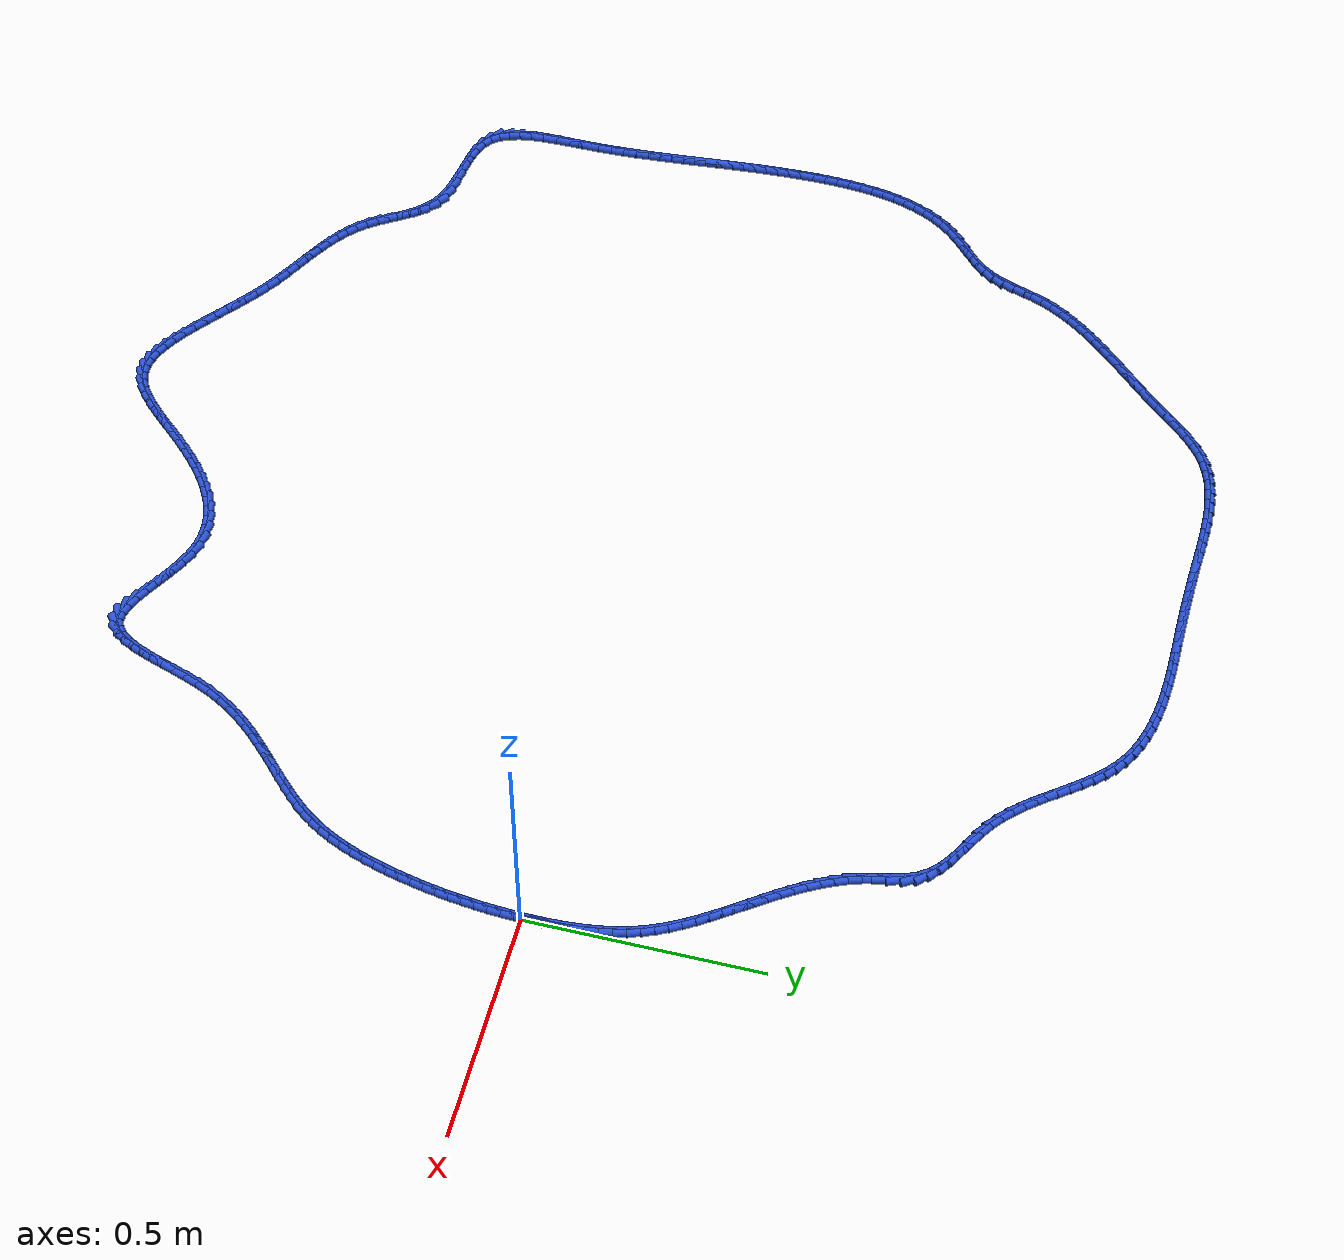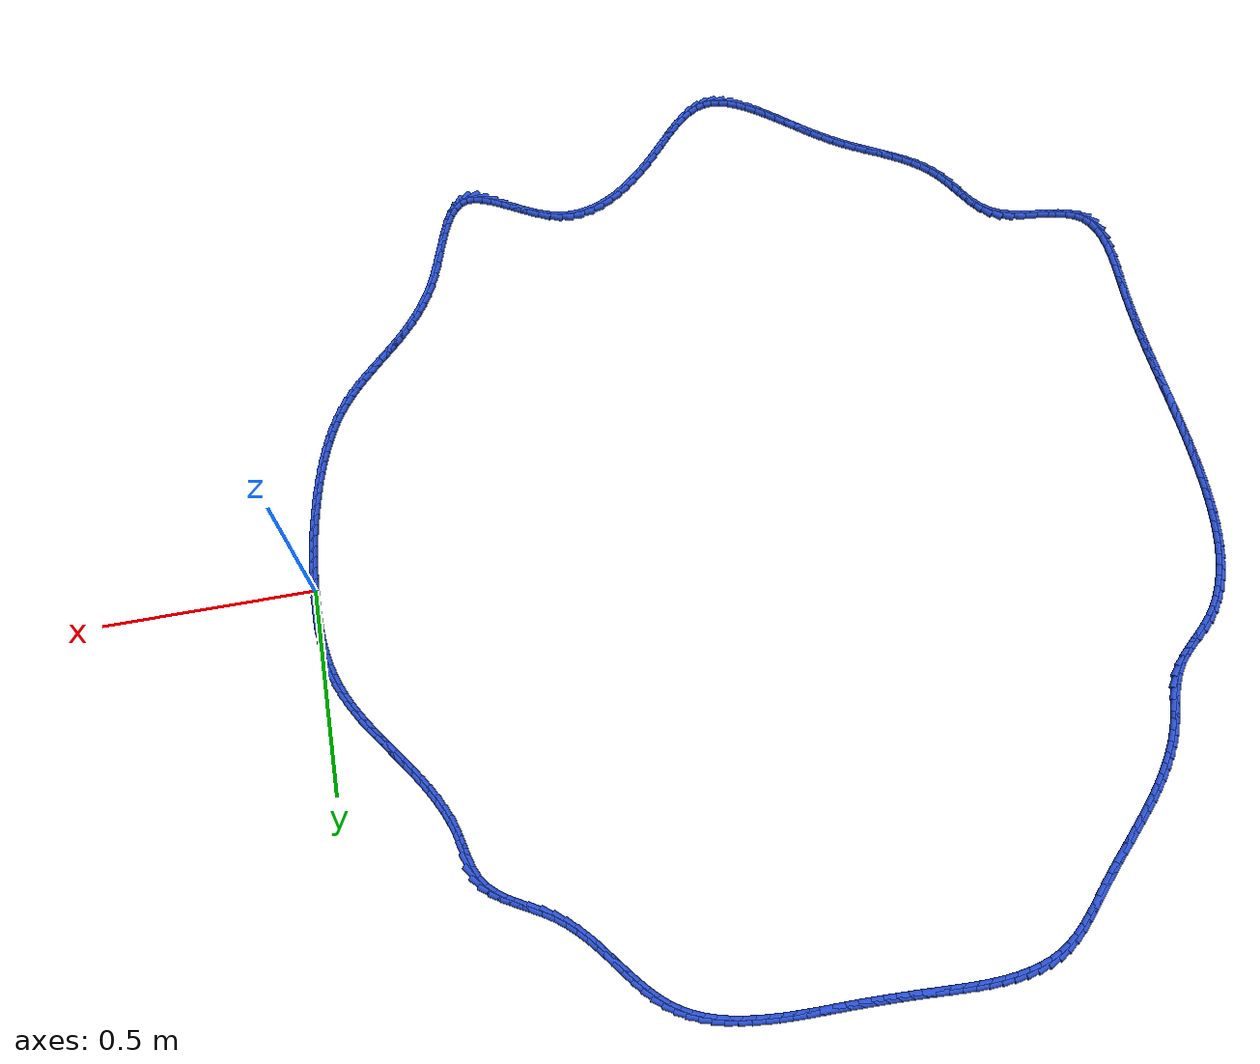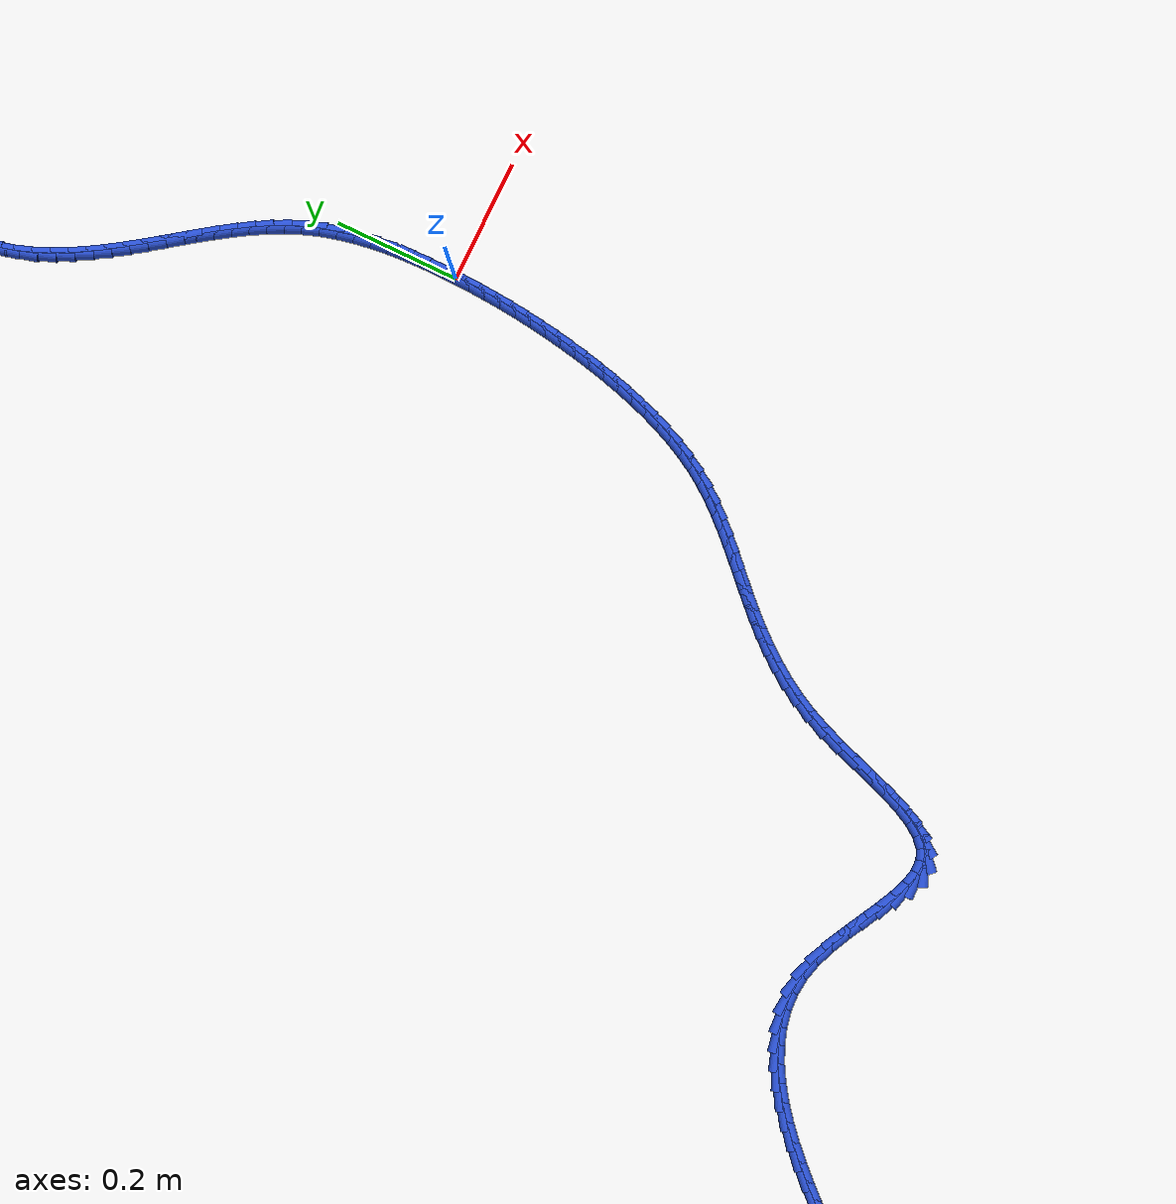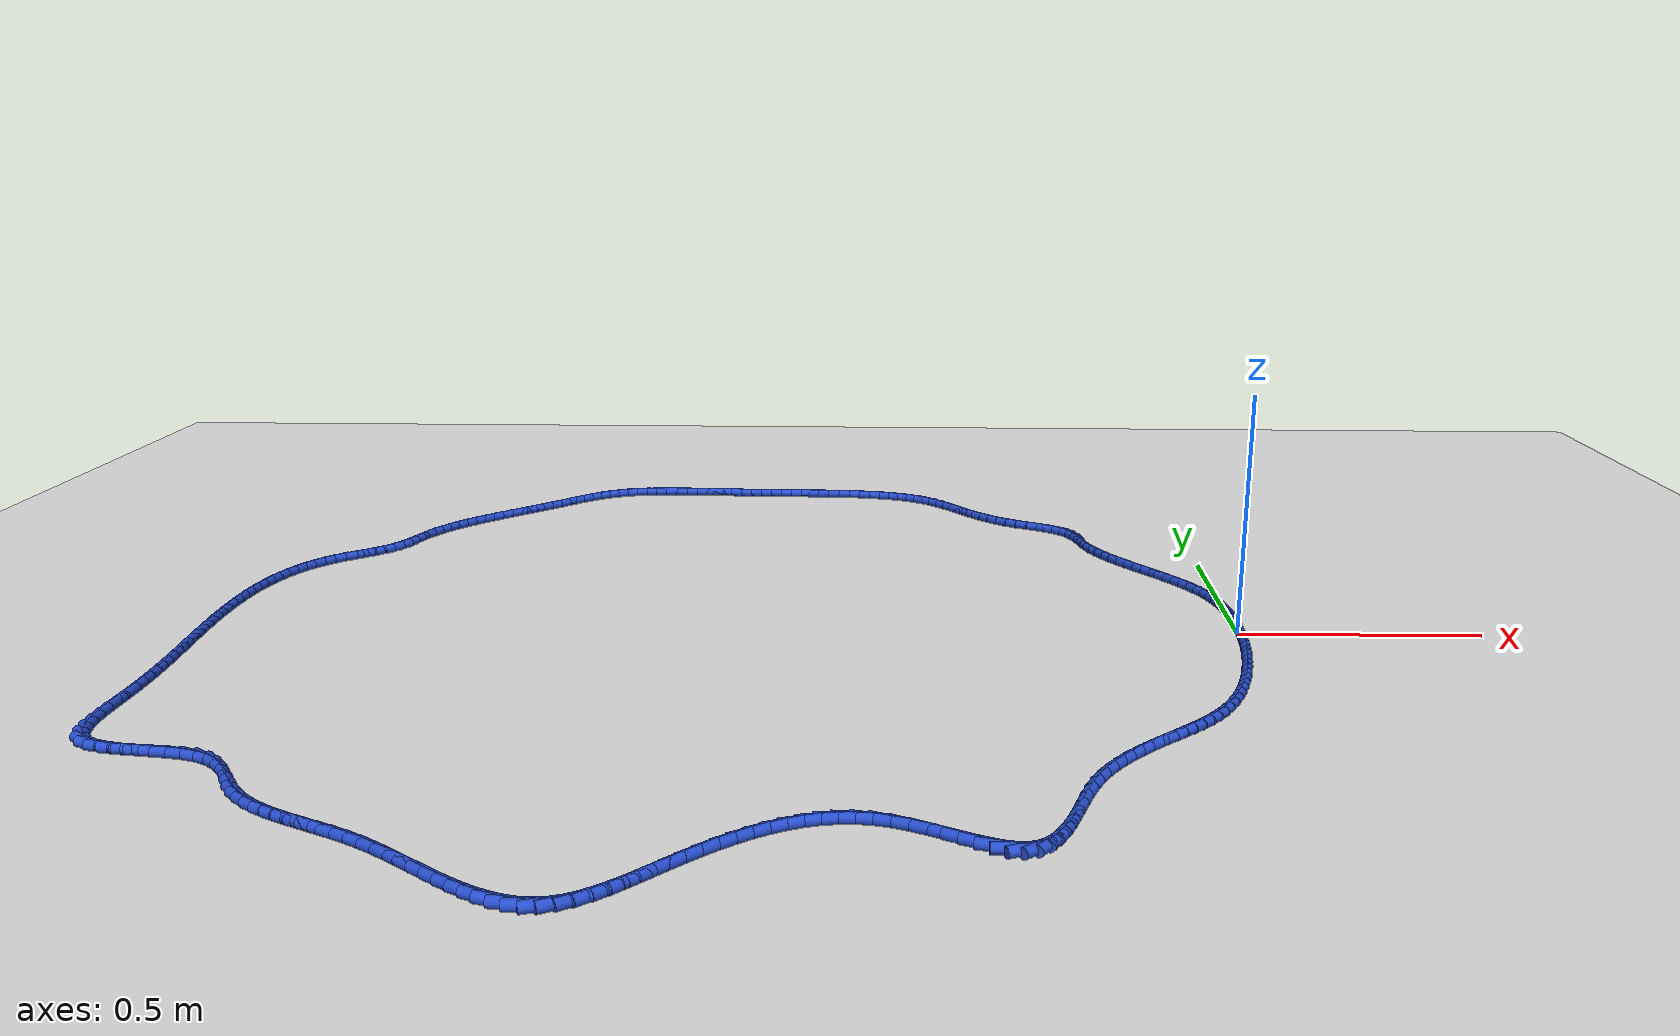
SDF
<sdf version="1.6">
 <world name="default">
  <light name="sun" type="directional">
   <pose>0 0 10 0 -0 0</pose>
   <diffuse>0.8 0.8 0.8 1</diffuse>
   <specular>0.2 0.2 0.2 1</specular>
   <attenuation>
    <range>1000</range>
    <constant>0.9</constant>
    <linear>0.01</linear>
    <quadratic>0.001</quadratic>
   </attenuation>
   <direction>-0.5 0.1 -0.9</direction>
  </light>
  <model name="ground_plane">
   <static>1</static>
   <link name="link">
    <collision name="collision">
     <geometry><plane><normal>0 0 1</normal><size>100 100</size></plane></geometry>
     <surface><friction><ode><mu>100</mu><mu2>50</mu2></ode></friction></surface>
    </collision>
    <visual name="visual">
     <cast_shadows>0</cast_shadows>
     <geometry><plane><normal>0 0 1</normal><size>100 100</size></plane></geometry>
     <material>
      <script><uri>file://media/materials/scripts/gazebo.material</uri><name>Gazebo/WhiteGlow</name></script>
     </material>
    </visual>
   </link>
  </model>
  <gravity>0 0 -9.8</gravity>
  <magnetic_field>6e-06 2.3e-05 -4.2e-05</magnetic_field>
  <atmosphere type="adiabatic"/>
  <physics name="default_physics" default="0" type="ode">
   <max_step_size>0.001</max_step_size>
   <real_time_factor>1</real_time_factor>
   <real_time_update_rate>1000</real_time_update_rate>
  </physics>
  <scene><ambient>0.4 0.4 0.4 1</ambient><background>0.7 0.7 0.7 1</background><shadows>1</shadows></scene>
  <spherical_coordinates>
   <surface_model>EARTH_WGS84</surface_model>
   <latitude_deg>0</latitude_deg>
   <longitude_deg>0</longitude_deg>
   <elevation>0</elevation>
   <heading_deg>0</heading_deg>
  </spherical_coordinates>
  <model name="line">
   <link name="link_0">
    <pose>-9.107298248878237e-18 4.163336342344337e-17 0.01 0 1.57 1.551484172950166</pose>
    <collision name="collision">
     <geometry><cylinder><radius>0.01</radius><length>0.08</length></cylinder></geometry>
    </collision>
    <visual name="visual">
     <material>
      <script><name>Gazebo/Blue</name><uri>file://media/materials/scripts/gazebo.material</uri></script>
     </material>
     <geometry><cylinder><radius>0.01</radius><length>0.08</length></cylinder></geometry>
    </visual>
   </link>
   <link name="link_1">
    <pose>0.0005427913405773272 0.02810271001218487 0.01 0 1.57 -1.565745009043975</pose>
    <collision name="collision">
     <geometry><cylinder><radius>0.01</radius><length>0.08</length></cylinder></geometry>
    </collision>
    <visual name="visual">
     <material>
      <script><name>Gazebo/Blue</name><uri>file://media/materials/scripts/gazebo.material</uri></script>
     </material>
     <geometry><cylinder><radius>0.01</radius><length>0.08</length></cylinder></geometry>
    </visual>
   </link>
   <link name="link_2">
    <pose>0.00040029658367146204 0.05631189264009979 0.01 0 1.57 -1.5363101366053682</pose>
    <collision name="collision">
     <geometry><cylinder><radius>0.01</radius><length>0.08</length></cylinder></geometry>
    </collision>
    <visual name="visual">
     <material>
      <script><name>Gazebo/Blue</name><uri>file://media/materials/scripts/gazebo.material</uri></script>
     </material>
     <geometry><cylinder><radius>0.01</radius><length>0.08</length></cylinder></geometry>
    </visual>
   </link>
   <link name="link_3">
    <pose>-0.0005725924026010101 0.08451168118131286 0.01 0 1.57 -1.5015067465468235</pose>
    <collision name="collision">
     <geometry><cylinder><radius>0.01</radius><length>0.08</length></cylinder></geometry>
    </collision>
    <visual name="visual">
     <material>
      <script><name>Gazebo/Blue</name><uri>file://media/materials/scripts/gazebo.material</uri></script>
     </material>
     <geometry><cylinder><radius>0.01</radius><length>0.08</length></cylinder></geometry>
    </visual>
   </link>
   <link name="link_4">
    <pose>-0.002520983750123495 0.1125862089333922 0.01 0 1.57 -1.4609766809511677</pose>
    <collision name="collision">
     <geometry><cylinder><radius>0.01</radius><length>0.08</length></cylinder></geometry>
    </collision>
    <visual name="visual">
     <material>
      <script><name>Gazebo/Blue</name><uri>file://media/materials/scripts/gazebo.material</uri></script>
     </material>
     <geometry><cylinder><radius>0.01</radius><length>0.08</length></cylinder></geometry>
    </visual>
   </link>
   <link name="link_5">
    <pose>-0.005589985590779398 0.14041960919390578 0.01 0 1.57 -1.414324397645262</pose>
    <collision name="collision">
     <geometry><cylinder><radius>0.01</radius><length>0.08</length></cylinder></geometry>
    </collision>
    <visual name="visual">
     <material>
      <script><name>Gazebo/Blue</name><uri>file://media/materials/scripts/gazebo.material</uri></script>
     </material>
     <geometry><cylinder><radius>0.01</radius><length>0.08</length></cylinder></geometry>
    </visual>
   </link>
   <link name="link_6">
    <pose>-0.009924706056452128 0.16789601526042172 0.01 0 1.57 -1.3611525101138615</pose>
    <collision name="collision">
     <geometry><cylinder><radius>0.01</radius><length>0.08</length></cylinder></geometry>
    </collision>
    <visual name="visual">
     <material>
      <script><name>Gazebo/Blue</name><uri>file://media/materials/scripts/gazebo.material</uri></script>
     </material>
     <geometry><cylinder><radius>0.01</radius><length>0.08</length></cylinder></geometry>
    </visual>
   </link>
   <link name="link_7">
    <pose>-0.015670253279025083 0.19489956043050793 0.01 0 1.57 -1.3011140120505347</pose>
    <collision name="collision">
     <geometry><cylinder><radius>0.01</radius><length>0.08</length></cylinder></geometry>
    </collision>
    <visual name="visual">
     <material>
      <script><name>Gazebo/Blue</name><uri>file://media/materials/scripts/gazebo.material</uri></script>
     </material>
     <geometry><cylinder><radius>0.01</radius><length>0.08</length></cylinder></geometry>
    </visual>
   </link>
   <link name="link_8">
    <pose>-0.022971735390381675 0.22131437800173268 0.01 0 1.57 -1.234057572113319</pose>
    <collision name="collision">
     <geometry><cylinder><radius>0.01</radius><length>0.08</length></cylinder></geometry>
    </collision>
    <visual name="visual">
     <material>
      <script><name>Gazebo/Blue</name><uri>file://media/materials/scripts/gazebo.material</uri></script>
     </material>
     <geometry><cylinder><radius>0.01</radius><length>0.08</length></cylinder></geometry>
    </visual>
   </link>
   <link name="link_9">
    <pose>-0.03197252396105613 0.2470256445715553 0.01 0 1.57 -1.1655607419627865</pose>
    <collision name="collision">
     <geometry><cylinder><radius>0.01</radius><length>0.08</length></cylinder></geometry>
    </collision>
    <visual name="visual">
     <material>
      <script><name>Gazebo/Blue</name><uri>file://media/materials/scripts/gazebo.material</uri></script>
     </material>
     <geometry><cylinder><radius>0.01</radius><length>0.08</length></cylinder></geometry>
    </visual>
   </link>
   <link name="link_10">
    <pose>-0.042684838785796576 0.2719973307480866 0.01 0 1.57 -1.1054644885469476</pose>
    <collision name="collision">
     <geometry><cylinder><radius>0.01</radius><length>0.08</length></cylinder></geometry>
    </collision>
    <visual name="visual">
     <material>
      <script><name>Gazebo/Blue</name><uri>file://media/materials/scripts/gazebo.material</uri></script>
     </material>
     <geometry><cylinder><radius>0.01</radius><length>0.08</length></cylinder></geometry>
    </visual>
   </link>
   <link name="link_11">
    <pose>-0.054900380949217856 0.2963258914576315 0.01 0 1.57 -1.055064962549709</pose>
    <collision name="collision">
     <geometry><cylinder><radius>0.01</radius><length>0.08</length></cylinder></geometry>
    </collision>
    <visual name="visual">
     <material>
      <script><name>Gazebo/Blue</name><uri>file://media/materials/scripts/gazebo.material</uri></script>
     </material>
     <geometry><cylinder><radius>0.01</radius><length>0.08</length></cylinder></geometry>
    </visual>
   </link>
   <link name="link_12">
    <pose>-0.06838971442847842 0.3201204804821537 0.01 0 1.57 -1.0144284640028725</pose>
    <collision name="collision">
     <geometry><cylinder><radius>0.01</radius><length>0.08</length></cylinder></geometry>
    </collision>
    <visual name="visual">
     <material>
      <script><name>Gazebo/Blue</name><uri>file://media/materials/scripts/gazebo.material</uri></script>
     </material>
     <geometry><cylinder><radius>0.01</radius><length>0.08</length></cylinder></geometry>
    </visual>
   </link>
   <link name="link_13">
    <pose>-0.08292340320073685 0.3434902516036167 0.01 0 1.57 -0.9834184994799567</pose>
    <collision name="collision">
     <geometry><cylinder><radius>0.01</radius><length>0.08</length></cylinder></geometry>
    </collision>
    <visual name="visual">
     <material>
      <script><name>Gazebo/Blue</name><uri>file://media/materials/scripts/gazebo.material</uri></script>
     </material>
     <geometry><cylinder><radius>0.01</radius><length>0.08</length></cylinder></geometry>
    </visual>
   </link>
   <link name="link_14">
    <pose>-0.0982720112431516 0.366544358603984 0.01 0 1.57 -0.9618122379678639</pose>
    <collision name="collision">
     <geometry><cylinder><radius>0.01</radius><length>0.08</length></cylinder></geometry>
    </collision>
    <visual name="visual">
     <material>
      <script><name>Gazebo/Blue</name><uri>file://media/materials/scripts/gazebo.material</uri></script>
     </material>
     <geometry><cylinder><radius>0.01</radius><length>0.08</length></cylinder></geometry>
    </visual>
   </link>
   <link name="link_15">
    <pose>-0.11420610253288122 0.38939195526521914 0.01 0 1.57 -0.9493845383832721</pose>
    <collision name="collision">
     <geometry><cylinder><radius>0.01</radius><length>0.08</length></cylinder></geometry>
    </collision>
    <visual name="visual">
     <material>
      <script><name>Gazebo/Blue</name><uri>file://media/materials/scripts/gazebo.material</uri></script>
     </material>
     <geometry><cylinder><radius>0.01</radius><length>0.08</length></cylinder></geometry>
    </visual>
   </link>
   <link name="link_16">
    <pose>-0.13049624104708418 0.4121421953692855 0.01 0 1.57 -0.945961211068427</pose>
    <collision name="collision">
     <geometry><cylinder><radius>0.01</radius><length>0.08</length></cylinder></geometry>
    </collision>
    <visual name="visual">
     <material>
      <script><name>Gazebo/Blue</name><uri>file://media/materials/scripts/gazebo.material</uri></script>
     </material>
     <geometry><cylinder><radius>0.01</radius><length>0.08</length></cylinder></geometry>
    </visual>
   </link>
   <link name="link_17">
    <pose>-0.14691299076291903 0.43490423269814693 0.01 0 1.57 -0.9514463935267233</pose>
    <collision name="collision">
     <geometry><cylinder><radius>0.01</radius><length>0.08</length></cylinder></geometry>
    </collision>
    <visual name="visual">
     <material>
      <script><name>Gazebo/Blue</name><uri>file://media/materials/scripts/gazebo.material</uri></script>
     </material>
     <geometry><cylinder><radius>0.01</radius><length>0.08</length></cylinder></geometry>
    </visual>
   </link>
   <link name="link_18">
    <pose>-0.16322691565754427 0.45778722103376657 0.01 0 1.57 -0.965828306093649</pose>
    <collision name="collision">
     <geometry><cylinder><radius>0.01</radius><length>0.08</length></cylinder></geometry>
    </collision>
    <visual name="visual">
     <material>
      <script><name>Gazebo/Blue</name><uri>file://media/materials/scripts/gazebo.material</uri></script>
     </material>
     <geometry><cylinder><radius>0.01</radius><length>0.08</length></cylinder></geometry>
    </visual>
   </link>
   <link name="link_19">
    <pose>-0.17920857970811843 0.4809003141581081 0.01 0 1.57 -0.9891653862440924</pose>
    <collision name="collision">
     <geometry><cylinder><radius>0.01</radius><length>0.08</length></cylinder></geometry>
    </collision>
    <visual name="visual">
     <material>
      <script><name>Gazebo/Blue</name><uri>file://media/materials/scripts/gazebo.material</uri></script>
     </material>
     <geometry><cylinder><radius>0.01</radius><length>0.08</length></cylinder></geometry>
    </visual>
   </link>
   <link name="link_20">
    <pose>-0.19462854689179998 0.504352665853135 0.01 0 1.57 -1.0215523020878132</pose>
    <collision name="collision">
     <geometry><cylinder><radius>0.01</radius><length>0.08</length></cylinder></geometry>
    </collision>
    <visual name="visual">
     <material>
      <script><name>Gazebo/Blue</name><uri>file://media/materials/scripts/gazebo.material</uri></script>
     </material>
     <geometry><cylinder><radius>0.01</radius><length>0.08</length></cylinder></geometry>
    </visual>
   </link>
   <link name="link_21">
    <pose>-0.20925738118574744 0.5282534299008108 0.01 0 1.57 -1.063063683374744</pose>
    <collision name="collision">
     <geometry><cylinder><radius>0.01</radius><length>0.08</length></cylinder></geometry>
    </collision>
    <visual name="visual">
     <material>
      <script><name>Gazebo/Blue</name><uri>file://media/materials/scripts/gazebo.material</uri></script>
     </material>
     <geometry><cylinder><radius>0.01</radius><length>0.08</length></cylinder></geometry>
    </visual>
   </link>
   <link name="link_22">
    <pose>-0.22286564656711938 0.5527117600830993 0.01 0 1.57 -1.1136737793806426</pose>
    <collision name="collision">
     <geometry><cylinder><radius>0.01</radius><length>0.08</length></cylinder></geometry>
    </collision>
    <visual name="visual">
     <material>
      <script><name>Gazebo/Blue</name><uri>file://media/materials/scripts/gazebo.material</uri></script>
     </material>
     <geometry><cylinder><radius>0.01</radius><length>0.08</length></cylinder></geometry>
    </visual>
   </link>
   <link name="link_23">
    <pose>-0.23522390701307427 0.5778368101819635 0.01 0 1.57 -1.1731541740522073</pose>
    <collision name="collision">
     <geometry><cylinder><radius>0.01</radius><length>0.08</length></cylinder></geometry>
    </collision>
    <visual name="visual">
     <material>
      <script><name>Gazebo/Blue</name><uri>file://media/materials/scripts/gazebo.material</uri></script>
     </material>
     <geometry><cylinder><radius>0.01</radius><length>0.08</length></cylinder></geometry>
    </visual>
   </link>
   <link name="link_24">
    <pose>-0.24610272650077059 0.6037377339793673 0.01 0 1.57 -1.24096045702606</pose>
    <collision name="collision">
     <geometry><cylinder><radius>0.01</radius><length>0.08</length></cylinder></geometry>
    </collision>
    <visual name="visual">
     <material>
      <script><name>Gazebo/Blue</name><uri>file://media/materials/scripts/gazebo.material</uri></script>
     </material>
     <geometry><cylinder><radius>0.01</radius><length>0.08</length></cylinder></geometry>
    </visual>
   </link>
   <link name="link_25">
    <pose>-0.25527266900736684 0.630523685257274 0.01 0 1.57 -1.3113827533540725</pose>
    <collision name="collision">
     <geometry><cylinder><radius>0.01</radius><length>0.08</length></cylinder></geometry>
    </collision>
    <visual name="visual">
     <material>
      <script><name>Gazebo/Blue</name><uri>file://media/materials/scripts/gazebo.material</uri></script>
     </material>
     <geometry><cylinder><radius>0.01</radius><length>0.08</length></cylinder></geometry>
    </visual>
   </link>
   <link name="link_26">
    <pose>-0.2626243480211201 0.65822471452186 0.01 0 1.57 -1.3376726835134465</pose>
    <collision name="collision">
     <geometry><cylinder><radius>0.01</radius><length>0.08</length></cylinder></geometry>
    </collision>
    <visual name="visual">
     <material>
      <script><name>Gazebo/Blue</name><uri>file://media/materials/scripts/gazebo.material</uri></script>
     </material>
     <geometry><cylinder><radius>0.01</radius><length>0.08</length></cylinder></geometry>
    </visual>
   </link>
   <link name="link_27">
    <pose>-0.2692397196739341 0.6860858702844164 0.01 0 1.57 -1.2931679342303561</pose>
    <collision name="collision">
     <geometry><cylinder><radius>0.01</radius><length>0.08</length></cylinder></geometry>
    </collision>
    <visual name="visual">
     <material>
      <script><name>Gazebo/Blue</name><uri>file://media/materials/scripts/gazebo.material</uri></script>
     </material>
     <geometry><cylinder><radius>0.01</radius><length>0.08</length></cylinder></geometry>
    </visual>
   </link>
   <link name="link_28">
    <pose>-0.2768823166532206 0.7129030952019313 0.01 0 1.57 -1.1688672299421539</pose>
    <collision name="collision">
     <geometry><cylinder><radius>0.01</radius><length>0.08</length></cylinder></geometry>
    </collision>
    <visual name="visual">
     <material>
      <script><name>Gazebo/Blue</name><uri>file://media/materials/scripts/gazebo.material</uri></script>
     </material>
     <geometry><cylinder><radius>0.01</radius><length>0.08</length></cylinder></geometry>
    </visual>
   </link>
   <link name="link_29">
    <pose>-0.2873236914929968 0.7374670474772387 0.01 0 1.57 -0.9625971926734253</pose>
    <collision name="collision">
     <geometry><cylinder><radius>0.01</radius><length>0.08</length></cylinder></geometry>
    </collision>
    <visual name="visual">
     <material>
      <script><name>Gazebo/Blue</name><uri>file://media/materials/scripts/gazebo.material</uri></script>
     </material>
     <geometry><cylinder><radius>0.01</radius><length>0.08</length></cylinder></geometry>
    </visual>
   </link>
   <link name="link_30">
    <pose>-0.3021240761465666 0.7587245869912512 0.01 0 1.57 -0.7636432868093413</pose>
    <collision name="collision">
     <geometry><cylinder><radius>0.01</radius><length>0.08</length></cylinder></geometry>
    </collision>
    <visual name="visual">
     <material>
      <script><name>Gazebo/Blue</name><uri>file://media/materials/scripts/gazebo.material</uri></script>
     </material>
     <geometry><cylinder><radius>0.01</radius><length>0.08</length></cylinder></geometry>
    </visual>
   </link>
   <link name="link_31">
    <pose>-0.32111128002613154 0.7769031271192484 0.01 0 1.57 -0.6241413143283348</pose>
    <collision name="collision">
     <geometry><cylinder><radius>0.01</radius><length>0.08</length></cylinder></geometry>
    </collision>
    <visual name="visual">
     <material>
      <script><name>Gazebo/Blue</name><uri>file://media/materials/scripts/gazebo.material</uri></script>
     </material>
     <geometry><cylinder><radius>0.01</radius><length>0.08</length></cylinder></geometry>
    </visual>
   </link>
   <link name="link_32">
    <pose>-0.3432644490844522 0.7928573871810703 0.01 0 1.57 -0.5408287048338407</pose>
    <collision name="collision">
     <geometry><cylinder><radius>0.01</radius><length>0.08</length></cylinder></geometry>
    </collision>
    <visual name="visual">
     <material>
      <script><name>Gazebo/Blue</name><uri>file://media/materials/scripts/gazebo.material</uri></script>
     </material>
     <geometry><cylinder><radius>0.01</radius><length>0.08</length></cylinder></geometry>
    </visual>
   </link>
   <link name="link_33">
    <pose>-0.3675569112519301 0.807446386999863 0.01 0 1.57 -0.5061602920310745</pose>
    <collision name="collision">
     <geometry><cylinder><radius>0.01</radius><length>0.08</length></cylinder></geometry>
    </collision>
    <visual name="visual">
     <material>
      <script><name>Gazebo/Blue</name><uri>file://media/materials/scripts/gazebo.material</uri></script>
     </material>
     <geometry><cylinder><radius>0.01</radius><length>0.08</length></cylinder></geometry>
    </visual>
   </link>
   <link name="link_34">
    <pose>-0.3929619944589669 0.821529146398772 0.01 0 1.57 -0.5152704477597619</pose>
    <collision name="collision">
     <geometry><cylinder><radius>0.01</radius><length>0.08</length></cylinder></geometry>
    </collision>
    <visual name="visual">
     <material>
      <script><name>Gazebo/Blue</name><uri>file://media/materials/scripts/gazebo.material</uri></script>
     </material>
     <geometry><cylinder><radius>0.01</radius><length>0.08</length></cylinder></geometry>
    </visual>
   </link>
   <link name="link_35">
    <pose>-0.4184530266359636 0.8359646852009417 0.01 0 1.57 -0.5674367135877375</pose>
    <collision name="collision">
     <geometry><cylinder><radius>0.01</radius><length>0.08</length></cylinder></geometry>
    </collision>
    <visual name="visual">
     <material>
      <script><name>Gazebo/Blue</name><uri>file://media/materials/scripts/gazebo.material</uri></script>
     </material>
     <geometry><cylinder><radius>0.01</radius><length>0.08</length></cylinder></geometry>
    </visual>
   </link>
   <link name="link_36">
    <pose>-0.44300333571332207 0.8516120232295181 0.01 0 1.57 -0.656594400091862</pose>
    <collision name="collision">
     <geometry><cylinder><radius>0.01</radius><length>0.08</length></cylinder></geometry>
    </collision>
    <visual name="visual">
     <material>
      <script><name>Gazebo/Blue</name><uri>file://media/materials/scripts/gazebo.material</uri></script>
     </material>
     <geometry><cylinder><radius>0.01</radius><length>0.08</length></cylinder></geometry>
    </visual>
   </link>
   <link name="link_37">
    <pose>-0.4657708135645299 0.8691580612607689 0.01 0 1.57 -0.7422710341360119</pose>
    <collision name="collision">
     <geometry><cylinder><radius>0.01</radius><length>0.08</length></cylinder></geometry>
    </collision>
    <visual name="visual">
     <material>
      <script><name>Gazebo/Blue</name><uri>file://media/materials/scripts/gazebo.material</uri></script>
     </material>
     <geometry><cylinder><radius>0.01</radius><length>0.08</length></cylinder></geometry>
    </visual>
   </link>
   <link name="link_38">
    <pose>-0.48680837306795843 0.8884550291177987 0.01 0 1.57 -0.8106165457230103</pose>
    <collision name="collision">
     <geometry><cylinder><radius>0.01</radius><length>0.08</length></cylinder></geometry>
    </collision>
    <visual name="visual">
     <material>
      <script><name>Gazebo/Blue</name><uri>file://media/materials/scripts/gazebo.material</uri></script>
     </material>
     <geometry><cylinder><radius>0.01</radius><length>0.08</length></cylinder></geometry>
    </visual>
   </link>
   <link name="link_39">
    <pose>-0.5064398553271532 0.9091024967210815 0.01 0 1.57 -0.8611785684220311</pose>
    <collision name="collision">
     <geometry><cylinder><radius>0.01</radius><length>0.08</length></cylinder></geometry>
    </collision>
    <visual name="visual">
     <material>
      <script><name>Gazebo/Blue</name><uri>file://media/materials/scripts/gazebo.material</uri></script>
     </material>
     <geometry><cylinder><radius>0.01</radius><length>0.08</length></cylinder></geometry>
    </visual>
   </link>
   <link name="link_40">
    <pose>-0.5249891605470319 0.930699978874843 0.01 0 1.57 -0.8940372588538208</pose>
    <collision name="collision">
     <geometry><cylinder><radius>0.01</radius><length>0.08</length></cylinder></geometry>
    </collision>
    <visual name="visual">
     <material>
      <script><name>Gazebo/Blue</name><uri>file://media/materials/scripts/gazebo.material</uri></script>
     </material>
     <geometry><cylinder><radius>0.01</radius><length>0.08</length></cylinder></geometry>
    </visual>
   </link>
   <link name="link_41">
    <pose>-0.5427801889325138 0.9528469903833117 0.01 0 1.57 -0.9093264269095521</pose>
    <collision name="collision">
     <geometry><cylinder><radius>0.01</radius><length>0.08</length></cylinder></geometry>
    </collision>
    <visual name="visual">
     <material>
      <script><name>Gazebo/Blue</name><uri>file://media/materials/scripts/gazebo.material</uri></script>
     </material>
     <geometry><cylinder><radius>0.01</radius><length>0.08</length></cylinder></geometry>
    </visual>
   </link>
   <link name="link_42">
    <pose>-0.5601368406885167 0.9751430460507136 0.01 0 1.57 -0.9069226876301162</pose>
    <collision name="collision">
     <geometry><cylinder><radius>0.01</radius><length>0.08</length></cylinder></geometry>
    </collision>
    <visual name="visual">
     <material>
      <script><name>Gazebo/Blue</name><uri>file://media/materials/scripts/gazebo.material</uri></script>
     </material>
     <geometry><cylinder><radius>0.01</radius><length>0.08</length></cylinder></geometry>
    </visual>
   </link>
   <link name="link_43">
    <pose>-0.5773830160199588 0.9971876606812755 0.01 0 1.57 -0.8862863287968417</pose>
    <collision name="collision">
     <geometry><cylinder><radius>0.01</radius><length>0.08</length></cylinder></geometry>
    </collision>
    <visual name="visual">
     <material>
      <script><name>Gazebo/Blue</name><uri>file://media/materials/scripts/gazebo.material</uri></script>
     </material>
     <geometry><cylinder><radius>0.01</radius><length>0.08</length></cylinder></geometry>
    </visual>
   </link>
   <link name="link_44">
    <pose>-0.5948426151317584 1.018580349079224 0.01 0 1.57 -0.8464470127626167</pose>
    <collision name="collision">
     <geometry><cylinder><radius>0.01</radius><length>0.08</length></cylinder></geometry>
    </collision>
    <visual name="visual">
     <material>
      <script><name>Gazebo/Blue</name><uri>file://media/materials/scripts/gazebo.material</uri></script>
     </material>
     <geometry><cylinder><radius>0.01</radius><length>0.08</length></cylinder></geometry>
    </visual>
   </link>
   <link name="link_45">
    <pose>-0.6128395382288341 1.038920626048787 0.01 0 1.57 -0.7861726406434201</pose>
    <collision name="collision">
     <geometry><cylinder><radius>0.01</radius><length>0.08</length></cylinder></geometry>
    </collision>
    <visual name="visual">
     <material>
      <script><name>Gazebo/Blue</name><uri>file://media/materials/scripts/gazebo.material</uri></script>
     </material>
     <geometry><cylinder><radius>0.01</radius><length>0.08</length></cylinder></geometry>
    </visual>
   </link>
   <link name="link_46">
    <pose>-0.6316976855161038 1.0578080063941904 0.01 0 1.57 -0.7044134666287377</pose>
    <collision name="collision">
     <geometry><cylinder><radius>0.01</radius><length>0.08</length></cylinder></geometry>
    </collision>
    <visual name="visual">
     <material>
      <script><name>Gazebo/Blue</name><uri>file://media/materials/scripts/gazebo.material</uri></script>
     </material>
     <geometry><cylinder><radius>0.01</radius><length>0.08</length></cylinder></geometry>
    </visual>
   </link>
   <link name="link_47">
    <pose>-0.6517409571984863 1.0748420049196608 0.01 0 1.57 -0.6025228184148906</pose>
    <collision name="collision">
     <geometry><cylinder><radius>0.01</radius><length>0.08</length></cylinder></geometry>
    </collision>
    <visual name="visual">
     <material>
      <script><name>Gazebo/Blue</name><uri>file://media/materials/scripts/gazebo.material</uri></script>
     </material>
     <geometry><cylinder><radius>0.01</radius><length>0.08</length></cylinder></geometry>
    </visual>
   </link>
   <link name="link_48">
    <pose>-0.6732698553087253 1.0896505891494355 0.01 0 1.57 -0.4987566623759975</pose>
    <collision name="collision">
     <geometry><cylinder><radius>0.01</radius><length>0.08</length></cylinder></geometry>
    </collision>
    <visual name="visual">
     <material>
      <script><name>Gazebo/Blue</name><uri>file://media/materials/scripts/gazebo.material</uri></script>
     </material>
     <geometry><cylinder><radius>0.01</radius><length>0.08</length></cylinder></geometry>
    </visual>
   </link>
   <link name="link_49">
    <pose>-0.696307548001608 1.1021989710352331 0.01 0 1.57 -0.40565415533101484</pose>
    <collision name="collision">
     <geometry><cylinder><radius>0.01</radius><length>0.08</length></cylinder></geometry>
    </collision>
    <visual name="visual">
     <material>
      <script><name>Gazebo/Blue</name><uri>file://media/materials/scripts/gazebo.material</uri></script>
     </material>
     <geometry><cylinder><radius>0.01</radius><length>0.08</length></cylinder></geometry>
    </visual>
   </link>
   <link name="link_50">
    <pose>-0.7206957144428275 1.1126730573485697 0.01 0 1.57 -0.323993584192527</pose>
    <collision name="collision">
     <geometry><cylinder><radius>0.01</radius><length>0.08</length></cylinder></geometry>
    </collision>
    <visual name="visual">
     <material>
      <script><name>Gazebo/Blue</name><uri>file://media/materials/scripts/gazebo.material</uri></script>
     </material>
     <geometry><cylinder><radius>0.01</radius><length>0.08</length></cylinder></geometry>
    </visual>
   </link>
   <link name="link_51">
    <pose>-0.7462728916771637 1.1212625757528683 0.01 0 1.57 -0.25357395761807516</pose>
    <collision name="collision">
     <geometry><cylinder><radius>0.01</radius><length>0.08</length></cylinder></geometry>
    </collision>
    <visual name="visual">
     <material>
      <script><name>Gazebo/Blue</name><uri>file://media/materials/scripts/gazebo.material</uri></script>
     </material>
     <geometry><cylinder><radius>0.01</radius><length>0.08</length></cylinder></geometry>
    </visual>
   </link>
   <link name="link_52">
    <pose>-0.7728776167493947 1.1281572539115508 0.01 0 1.57 -0.19373179015244635</pose>
    <collision name="collision">
     <geometry><cylinder><radius>0.01</radius><length>0.08</length></cylinder></geometry>
    </collision>
    <visual name="visual">
     <material>
      <script><name>Gazebo/Blue</name><uri>file://media/materials/scripts/gazebo.material</uri></script>
     </material>
     <geometry><cylinder><radius>0.01</radius><length>0.08</length></cylinder></geometry>
    </visual>
   </link>
   <link name="link_53">
    <pose>-0.8003484267042998 1.1335468194880398 0.01 0 1.57 -0.14360509545390757</pose>
    <collision name="collision">
     <geometry><cylinder><radius>0.01</radius><length>0.08</length></cylinder></geometry>
    </collision>
    <visual name="visual">
     <material>
      <script><name>Gazebo/Blue</name><uri>file://media/materials/scripts/gazebo.material</uri></script>
     </material>
     <geometry><cylinder><radius>0.01</radius><length>0.08</length></cylinder></geometry>
    </visual>
   </link>
   <link name="link_54">
    <pose>-0.8285238585866581 1.1376210001457565 0.01 0 1.57 -0.10231101858222692</pose>
    <collision name="collision">
     <geometry><cylinder><radius>0.01</radius><length>0.08</length></cylinder></geometry>
    </collision>
    <visual name="visual">
     <material>
      <script><name>Gazebo/Blue</name><uri>file://media/materials/scripts/gazebo.material</uri></script>
     </material>
     <geometry><cylinder><radius>0.01</radius><length>0.08</length></cylinder></geometry>
    </visual>
   </link>
   <link name="link_55">
    <pose>-0.8572424494412481 1.1405695235481246 0.01 0 1.57 -0.06905066343870814</pose>
    <collision name="collision">
     <geometry><cylinder><radius>0.01</radius><length>0.08</length></cylinder></geometry>
    </collision>
    <visual name="visual">
     <material>
      <script><name>Gazebo/Blue</name><uri>file://media/materials/scripts/gazebo.material</uri></script>
     </material>
     <geometry><cylinder><radius>0.01</radius><length>0.08</length></cylinder></geometry>
    </visual>
   </link>
   <link name="link_56">
    <pose>-0.8863427363128485 1.1425821173585649 0.01 0 1.57 -0.043164489737550306</pose>
    <collision name="collision">
     <geometry><cylinder><radius>0.01</radius><length>0.08</length></cylinder></geometry>
    </collision>
    <visual name="visual">
     <material>
      <script><name>Gazebo/Blue</name><uri>file://media/materials/scripts/gazebo.material</uri></script>
     </material>
     <geometry><cylinder><radius>0.01</radius><length>0.08</length></cylinder></geometry>
    </visual>
   </link>
   <link name="link_57">
    <pose>-0.9156632562462386 1.1438485092405002 0.01 0 1.57 -0.024159177852286832</pose>
    <collision name="collision">
     <geometry><cylinder><radius>0.01</radius><length>0.08</length></cylinder></geometry>
    </collision>
    <visual name="visual">
     <material>
      <script><name>Gazebo/Blue</name><uri>file://media/materials/scripts/gazebo.material</uri></script>
     </material>
     <geometry><cylinder><radius>0.01</radius><length>0.08</length></cylinder></geometry>
    </visual>
   </link>
   <link name="link_58">
    <pose>-0.9450425462861973 1.144558426857353 0.01 0 1.57 -0.011721147005447357</pose>
    <collision name="collision">
     <geometry><cylinder><radius>0.01</radius><length>0.08</length></cylinder></geometry>
    </collision>
    <visual name="visual">
     <material>
      <script><name>Gazebo/Blue</name><uri>file://media/materials/scripts/gazebo.material</uri></script>
     </material>
     <geometry><cylinder><radius>0.01</radius><length>0.08</length></cylinder></geometry>
    </visual>
   </link>
   <link name="link_59">
    <pose>-0.9743191434775033 1.144901597872545 0.01 0 1.57 -0.005726862427849469</pose>
    <collision name="collision">
     <geometry><cylinder><radius>0.01</radius><length>0.08</length></cylinder></geometry>
    </collision>
    <visual name="visual">
     <material>
      <script><name>Gazebo/Blue</name><uri>file://media/materials/scripts/gazebo.material</uri></script>
     </material>
     <geometry><cylinder><radius>0.01</radius><length>0.08</length></cylinder></geometry>
    </visual>
   </link>
   <link name="link_60">
    <pose>-1.0033315848649351 1.1450677499494981 0.01 0 1.57 -0.006255489113667665</pose>
    <collision name="collision">
     <geometry><cylinder><radius>0.01</radius><length>0.08</length></cylinder></geometry>
    </collision>
    <visual name="visual">
     <material>
      <script><name>Gazebo/Blue</name><uri>file://media/materials/scripts/gazebo.material</uri></script>
     </material>
     <geometry><cylinder><radius>0.01</radius><length>0.08</length></cylinder></geometry>
    </visual>
   </link>
   <link name="link_61">
    <pose>-1.031918464814238 1.1452465771983924 0.01 0 1.57 -0.012063305055428054</pose>
    <collision name="collision">
     <geometry><cylinder><radius>0.01</radius><length>0.08</length></cylinder></geometry>
    </collision>
    <visual name="visual">
     <material>
      <script><name>Gazebo/Blue</name><uri>file://media/materials/scripts/gazebo.material</uri></script>
     </material>
     <geometry><cylinder><radius>0.01</radius><length>0.08</length></cylinder></geometry>
    </visual>
   </link>
   <link name="link_62">
    <pose>-1.0599910377494666 1.145585241637419 0.01 0 1.57 -0.018777655697686864</pose>
    <collision name="collision">
     <geometry><cylinder><radius>0.01</radius><length>0.08</length></cylinder></geometry>
    </collision>
    <visual name="visual">
     <material>
      <script><name>Gazebo/Blue</name><uri>file://media/materials/scripts/gazebo.material</uri></script>
     </material>
     <geometry><cylinder><radius>0.01</radius><length>0.08</length></cylinder></geometry>
    </visual>
   </link>
   <link name="link_63">
    <pose>-1.0876753931300798 1.1461051500390338 0.01 0 1.57 -0.025463691716911725</pose>
    <collision name="collision">
     <geometry><cylinder><radius>0.01</radius><length>0.08</length></cylinder></geometry>
    </collision>
    <visual name="visual">
     <material>
      <script><name>Gazebo/Blue</name><uri>file://media/materials/scripts/gazebo.material</uri></script>
     </material>
     <geometry><cylinder><radius>0.01</radius><length>0.08</length></cylinder></geometry>
    </visual>
   </link>
   <link name="link_64">
    <pose>-1.1151371357905417 1.1468045785644083 0.01 0 1.57 -0.03199904647307054</pose>
    <collision name="collision">
     <geometry><cylinder><radius>0.01</radius><length>0.08</length></cylinder></geometry>
    </collision>
    <visual name="visual">
     <material>
      <script><name>Gazebo/Blue</name><uri>file://media/materials/scripts/gazebo.material</uri></script>
     </material>
     <geometry><cylinder><radius>0.01</radius><length>0.08</length></cylinder></geometry>
    </visual>
   </link>
   <link name="link_65">
    <pose>-1.1425418705653185 1.1476818033747134 0.01 0 1.57 -0.03826447295040134</pose>
    <collision name="collision">
     <geometry><cylinder><radius>0.01</radius><length>0.08</length></cylinder></geometry>
    </collision>
    <visual name="visual">
     <material>
      <script><name>Gazebo/Blue</name><uri>file://media/materials/scripts/gazebo.material</uri></script>
     </material>
     <geometry><cylinder><radius>0.01</radius><length>0.08</length></cylinder></geometry>
    </visual>
   </link>
   <link name="link_66">
    <pose>-1.1700552022888753 1.1487351006311202 0.01 0 1.57 -0.04415102445250128</pose>
    <collision name="collision">
     <geometry><cylinder><radius>0.01</radius><length>0.08</length></cylinder></geometry>
    </collision>
    <visual name="visual">
     <material>
      <script><name>Gazebo/Blue</name><uri>file://media/materials/scripts/gazebo.material</uri></script>
     </material>
     <geometry><cylinder><radius>0.01</radius><length>0.08</length></cylinder></geometry>
    </visual>
   </link>
   <link name="link_67">
    <pose>-1.1978427357956773 1.1499627464948001 0.01 0 1.57 -0.04946991345475288</pose>
    <collision name="collision">
     <geometry><cylinder><radius>0.01</radius><length>0.08</length></cylinder></geometry>
    </collision>
    <visual name="visual">
     <material>
      <script><name>Gazebo/Blue</name><uri>file://media/materials/scripts/gazebo.material</uri></script>
     </material>
     <geometry><cylinder><radius>0.01</radius><length>0.08</length></cylinder></geometry>
    </visual>
   </link>
   <link name="link_68">
    <pose>-1.2260663849839828 1.1513601080716547 0.01 0 1.57 -0.05043283540864319</pose>
    <collision name="collision">
     <geometry><cylinder><radius>0.01</radius><length>0.08</length></cylinder></geometry>
    </collision>
    <visual name="visual">
     <material>
      <script><name>Gazebo/Blue</name><uri>file://media/materials/scripts/gazebo.material</uri></script>
     </material>
     <geometry><cylinder><radius>0.01</radius><length>0.08</length></cylinder></geometry>
    </visual>
   </link>
   <link name="link_69">
    <pose>-1.2547421320679724 1.1528075346751712 0.01 0 1.57 -0.04236440016118949</pose>
    <collision name="collision">
     <geometry><cylinder><radius>0.01</radius><length>0.08</length></cylinder></geometry>
    </collision>
    <visual name="visual">
     <material>
      <script><name>Gazebo/Blue</name><uri>file://media/materials/scripts/gazebo.material</uri></script>
     </material>
     <geometry><cylinder><radius>0.01</radius><length>0.08</length></cylinder></geometry>
    </visual>
   </link>
   <link name="link_70">
    <pose>-1.2836949612115611 1.1540348382339194 0.01 0 1.57 -0.02502122624400573</pose>
    <collision name="collision">
     <geometry><cylinder><radius>0.01</radius><length>0.08</length></cylinder></geometry>
    </collision>
    <visual name="visual">
     <material>
      <script><name>Gazebo/Blue</name><uri>file://media/materials/scripts/gazebo.material</uri></script>
     </material>
     <geometry><cylinder><radius>0.01</radius><length>0.08</length></cylinder></geometry>
    </visual>
   </link>
   <link name="link_71">
    <pose>-1.3127369472310673 1.154761656020628 0.01 0 1.57 0.0018667810323370303</pose>
    <collision name="collision">
     <geometry><cylinder><radius>0.01</radius><length>0.08</length></cylinder></geometry>
    </collision>
    <visual name="visual">
     <material>
      <script><name>Gazebo/Blue</name><uri>file://media/materials/scripts/gazebo.material</uri></script>
     </material>
     <geometry><cylinder><radius>0.01</radius><length>0.08</length></cylinder></geometry>
    </visual>
   </link>
   <link name="link_72">
    <pose>-1.3416801649428103 1.1547076253080255 0.01 0 1.57 0.0388979278173846</pose>
    <collision name="collision">
     <geometry><cylinder><radius>0.01</radius><length>0.08</length></cylinder></geometry>
    </collision>
    <visual name="visual">
     <material>
      <script><name>Gazebo/Blue</name><uri>file://media/materials/scripts/gazebo.material</uri></script>
     </material>
     <geometry><cylinder><radius>0.01</radius><length>0.08</length></cylinder></geometry>
    </visual>
   </link>
   <link name="link_73">
    <pose>-1.37033668916311 1.1535923833688408 0.01 0 1.57 0.08695722552844928</pose>
    <collision name="collision">
     <geometry><cylinder><radius>0.01</radius><length>0.08</length></cylinder></geometry>
    </collision>
    <visual name="visual">
     <material>
      <script><name>Gazebo/Blue</name><uri>file://media/materials/scripts/gazebo.material</uri></script>
     </material>
     <geometry><cylinder><radius>0.01</radius><length>0.08</length></cylinder></geometry>
    </visual>
   </link>
   <link name="link_74">
    <pose>-1.398518594708286 1.1511355674758035 0.01 0 1.57 0.14714271772935733</pose>
    <collision name="collision">
     <geometry><cylinder><radius>0.01</radius><length>0.08</length></cylinder></geometry>
    </collision>
    <visual name="visual">
     <material>
      <script><name>Gazebo/Blue</name><uri>file://media/materials/scripts/gazebo.material</uri></script>
     </material>
     <geometry><cylinder><radius>0.01</radius><length>0.08</length></cylinder></geometry>
    </visual>
   </link>
   <link name="link_75">
    <pose>-1.4260379563946581 1.1470568149016411 0.01 0 1.57 0.22062020295751172</pose>
    <collision name="collision">
     <geometry><cylinder><radius>0.01</radius><length>0.08</length></cylinder></geometry>
    </collision>
    <visual name="visual">
     <material>
      <script><name>Gazebo/Blue</name><uri>file://media/materials/scripts/gazebo.material</uri></script>
     </material>
     <geometry><cylinder><radius>0.01</radius><length>0.08</length></cylinder></geometry>
    </visual>
   </link>
   <link name="link_76">
    <pose>-1.4527068490385449 1.141075762919083 0.01 0 1.57 0.3083558672227686</pose>
    <collision name="collision">
     <geometry><cylinder><radius>0.01</radius><length>0.08</length></cylinder></geometry>
    </collision>
    <visual name="visual">
     <material>
      <script><name>Gazebo/Blue</name><uri>file://media/materials/scripts/gazebo.material</uri></script>
     </material>
     <geometry><cylinder><radius>0.01</radius><length>0.08</length></cylinder></geometry>
    </visual>
   </link>
   <link name="link_77">
    <pose>-1.4783373474562664 1.1329120488008582 0.01 0 1.57 0.4106863981370692</pose>
    <collision name="collision">
     <geometry><cylinder><radius>0.01</radius><length>0.08</length></cylinder></geometry>
    </collision>
    <visual name="visual">
     <material>
      <script><name>Gazebo/Blue</name><uri>file://media/materials/scripts/gazebo.material</uri></script>
     </material>
     <geometry><cylinder><radius>0.01</radius><length>0.08</length></cylinder></geometry>
    </visual>
   </link>
   <link name="link_78">
    <pose>-1.5027415264641426 1.1222853098196948 0.01 0 1.57 0.5253655567180938</pose>
    <collision name="collision">
     <geometry><cylinder><radius>0.01</radius><length>0.08</length></cylinder></geometry>
    </collision>
    <visual name="visual">
     <material>
      <script><name>Gazebo/Blue</name><uri>file://media/materials/scripts/gazebo.material</uri></script>
     </material>
     <geometry><cylinder><radius>0.01</radius><length>0.08</length></cylinder></geometry>
    </visual>
   </link>
   <link name="link_79">
    <pose>-1.5257506155456224 1.1089467479432806 0.01 0 1.57 0.631430677718393</pose>
    <collision name="collision">
     <geometry><cylinder><radius>0.01</radius><length>0.08</length></cylinder></geometry>
    </collision>
    <visual name="visual">
     <material>
      <script><name>Gazebo/Blue</name><uri>file://media/materials/scripts/gazebo.material</uri></script>
     </material>
     <geometry><cylinder><radius>0.01</radius><length>0.08</length></cylinder></geometry>
    </visual>
   </link>
   <link name="link_80">
    <pose>-1.5474548016884604 1.0930742974116474 0.01 0 1.57 0.714171885106638</pose>
    <collision name="collision">
     <geometry><cylinder><radius>0.01</radius><length>0.08</length></cylinder></geometry>
    </collision>
    <visual name="visual">
     <material>
      <script><name>Gazebo/Blue</name><uri>file://media/materials/scripts/gazebo.material</uri></script>
     </material>
     <geometry><cylinder><radius>0.01</radius><length>0.08</length></cylinder></geometry>
    </visual>
   </link>
   <link name="link_81">
    <pose>-1.5681303585211297 1.07515254191011 0.01 0 1.57 0.7740421228602928</pose>
    <collision name="collision">
     <geometry><cylinder><radius>0.01</radius><length>0.08</length></cylinder></geometry>
    </collision>
    <visual name="visual">
     <material>
      <script><name>Gazebo/Blue</name><uri>file://media/materials/scripts/gazebo.material</uri></script>
     </material>
     <geometry><cylinder><radius>0.01</radius><length>0.08</length></cylinder></geometry>
    </visual>
   </link>
   <link name="link_82">
    <pose>-1.5880576394396537 1.0556727881130783 0.01 0 1.57 0.8125647109904394</pose>
    <collision name="collision">
     <geometry><cylinder><radius>0.01</radius><length>0.08</length></cylinder></geometry>
    </collision>
    <visual name="visual">
     <material>
      <script><name>Gazebo/Blue</name><uri>file://media/materials/scripts/gazebo.material</uri></script>
     </material>
     <geometry><cylinder><radius>0.01</radius><length>0.08</length></cylinder></geometry>
    </visual>
   </link>
   <link name="link_83">
    <pose>-1.6075169978400543 1.0351263426949595 0.01 0 1.57 0.8311665084110389</pose>
    <collision name="collision">
     <geometry><cylinder><radius>0.01</radius><length>0.08</length></cylinder></geometry>
    </collision>
    <visual name="visual">
     <material>
      <script><name>Gazebo/Blue</name><uri>file://media/materials/scripts/gazebo.material</uri></script>
     </material>
     <geometry><cylinder><radius>0.01</radius><length>0.08</length></cylinder></geometry>
    </visual>
   </link>
   <link name="link_84">
    <pose>-1.6267887871183548 1.0140045123301644 0.01 0 1.57 0.8307531167085646</pose>
    <collision name="collision">
     <geometry><cylinder><radius>0.01</radius><length>0.08</length></cylinder></geometry>
    </collision>
    <visual name="visual">
     <material>
      <script><name>Gazebo/Blue</name><uri>file://media/materials/scripts/gazebo.material</uri></script>
     </material>
     <geometry><cylinder><radius>0.01</radius><length>0.08</length></cylinder></geometry>
    </visual>
   </link>
   <link name="link_85">
    <pose>-1.646153360670578 0.9927986036931011 0.01 0 1.57 0.8148485012602998</pose>
    <collision name="collision">
     <geometry><cylinder><radius>0.01</radius><length>0.08</length></cylinder></geometry>
    </collision>
    <visual name="visual">
     <material>
      <script><name>Gazebo/Blue</name><uri>file://media/materials/scripts/gazebo.material</uri></script>
     </material>
     <geometry><cylinder><radius>0.01</radius><length>0.08</length></cylinder></geometry>
    </visual>
   </link>
   <link name="link_86">
    <pose>-1.6658357164576632 0.9719214100141447 0.01 0 1.57 0.7998124935140541</pose>
    <collision name="collision">
     <geometry><cylinder><radius>0.01</radius><length>0.08</length></cylinder></geometry>
    </collision>
    <visual name="visual">
     <material>
      <script><name>Gazebo/Blue</name><uri>file://media/materials/scripts/gazebo.material</uri></script>
     </material>
     <geometry><cylinder><radius>0.01</radius><length>0.08</length></cylinder></geometry>
    </visual>
   </link>
   <link name="link_87">
    <pose>-1.6857825871757295 0.9513910466702211 0.01 0 1.57 0.7908067574767592</pose>
    <collision name="collision">
     <geometry><cylinder><radius>0.01</radius><length>0.08</length></cylinder></geometry>
    </collision>
    <visual name="visual">
     <material>
      <script><name>Gazebo/Blue</name><uri>file://media/materials/scripts/gazebo.material</uri></script>
     </material>
     <geometry><cylinder><radius>0.01</radius><length>0.08</length></cylinder></geometry>
    </visual>
   </link>
   <link name="link_88">
    <pose>-1.7058534585161313 0.9311018821502511 0.01 0 1.57 0.7878681607909739</pose>
    <collision name="collision">
     <geometry><cylinder><radius>0.01</radius><length>0.08</length></cylinder></geometry>
    </collision>
    <visual name="visual">
     <material>
      <script><name>Gazebo/Blue</name><uri>file://media/materials/scripts/gazebo.material</uri></script>
     </material>
     <geometry><cylinder><radius>0.01</radius><length>0.08</length></cylinder></geometry>
    </visual>
   </link>
   <link name="link_89">
    <pose>-1.7259077854780778 0.9109482414109161 0.01 0 1.57 0.7910589872616692</pose>
    <collision name="collision">
     <geometry><cylinder><radius>0.01</radius><length>0.08</length></cylinder></geometry>
    </collision>
    <visual name="visual">
     <material>
      <script><name>Gazebo/Blue</name><uri>file://media/materials/scripts/gazebo.material</uri></script>
     </material>
     <geometry><cylinder><radius>0.01</radius><length>0.08</length></cylinder></geometry>
    </visual>
   </link>
   <link name="link_90">
    <pose>-1.7458050230607751 0.8908244494088965 0.01 0 1.57 0.8004730726590206</pose>
    <collision name="collision">
     <geometry><cylinder><radius>0.01</radius><length>0.08</length></cylinder></geometry>
    </collision>
    <visual name="visual">
     <material>
      <script><name>Gazebo/Blue</name><uri>file://media/materials/scripts/gazebo.material</uri></script>
     </material>
     <geometry><cylinder><radius>0.01</radius><length>0.08</length></cylinder></geometry>
    </visual>
   </link>
   <link name="link_91">
    <pose>-1.765404626263433 0.8706248311008731 0.01 0 1.57 0.8162335405163246</pose>
    <collision name="collision">
     <geometry><cylinder><radius>0.01</radius><length>0.08</length></cylinder></geometry>
    </collision>
    <visual name="visual">
     <material>
      <script><name>Gazebo/Blue</name><uri>file://media/materials/scripts/gazebo.material</uri></script>
     </material>
     <geometry><cylinder><radius>0.01</radius><length>0.08</length></cylinder></geometry>
    </visual>
   </link>
   <link name="link_92">
    <pose>-1.7845660500852585 0.8502437114435276 0.01 0 1.57 0.8384831141575659</pose>
    <collision name="collision">
     <geometry><cylinder><radius>0.01</radius><length>0.08</length></cylinder></geometry>
    </collision>
    <visual name="visual">
     <material>
      <script><name>Gazebo/Blue</name><uri>file://media/materials/scripts/gazebo.material</uri></script>
     </material>
     <geometry><cylinder><radius>0.01</radius><length>0.08</length></cylinder></geometry>
    </visual>
   </link>
   <link name="link_93">
    <pose>-1.8031487495254608 0.8295754153935412 0.01 0 1.57 0.8673657257531802</pose>
    <collision name="collision">
     <geometry><cylinder><radius>0.01</radius><length>0.08</length></cylinder></geometry>
    </collision>
    <visual name="visual">
     <material>
      <script><name>Gazebo/Blue</name><uri>file://media/materials/scripts/gazebo.material</uri></script>
     </material>
     <geometry><cylinder><radius>0.01</radius><length>0.08</length></cylinder></geometry>
    </visual>
   </link>
   <link name="link_94">
    <pose>-1.821012179583247 0.8085142679075943 0.01 0 1.57 0.9029979828976243</pose>
    <collision name="collision">
     <geometry><cylinder><radius>0.01</radius><length>0.08</length></cylinder></geometry>
    </collision>
    <visual name="visual">
     <material>
      <script><name>Gazebo/Blue</name><uri>file://media/materials/scripts/gazebo.material</uri></script>
     </material>
     <geometry><cylinder><radius>0.01</radius><length>0.08</length></cylinder></geometry>
    </visual>
   </link>
   <link name="link_95">
    <pose>-1.8380157952578262 0.7869545939423687 0.01 0 1.57 0.9454295222164931</pose>
    <collision name="collision">
     <geometry><cylinder><radius>0.01</radius><length>0.08</length></cylinder></geometry>
    </collision>
    <visual name="visual">
     <material>
      <script><name>Gazebo/Blue</name><uri>file://media/materials/scripts/gazebo.material</uri></script>
     </material>
     <geometry><cylinder><radius>0.01</radius><length>0.08</length></cylinder></geometry>
    </visual>
   </link>
   <link name="link_96">
    <pose>-1.8540190515484056 0.764790718454545 0.01 0 1.57 0.9945928305803479</pose>
    <collision name="collision">
     <geometry><cylinder><radius>0.01</radius><length>0.08</length></cylinder></geometry>
    </collision>
    <visual name="visual">
     <material>
      <script><name>Gazebo/Blue</name><uri>file://media/materials/scripts/gazebo.material</uri></script>
     </material>
     <geometry><cylinder><radius>0.01</radius><length>0.08</length></cylinder></geometry>
    </visual>
   </link>
   <link name="link_97">
    <pose>-1.8688814034541938 0.7419169664008043 0.01 0 1.57 1.050246149130082</pose>
    <collision name="collision">
     <geometry><cylinder><radius>0.01</radius><length>0.08</length></cylinder></geometry>
    </collision>
    <visual name="visual">
     <material>
      <script><name>Gazebo/Blue</name><uri>file://media/materials/scripts/gazebo.material</uri></script>
     </material>
     <geometry><cylinder><radius>0.01</radius><length>0.08</length></cylinder></geometry>
    </visual>
   </link>
   <link name="link_98">
    <pose>-1.8824623059743992 0.7182276627378277 0.01 0 1.57 1.1119175672216344</pose>
    <collision name="collision">
     <geometry><cylinder><radius>0.01</radius><length>0.08</length></cylinder></geometry>
    </collision>
    <visual name="visual">
     <material>
      <script><name>Gazebo/Blue</name><uri>file://media/materials/scripts/gazebo.material</uri></script>
     </material>
     <geometry><cylinder><radius>0.01</radius><length>0.08</length></cylinder></geometry>
    </visual>
   </link>
   <link name="link_99">
    <pose>-1.8946212141082297 0.693617132422296 0.01 0 1.57 1.1785381793979686</pose>
    <collision name="collision">
     <geometry><cylinder><radius>0.01</radius><length>0.08</length></cylinder></geometry>
    </collision>
    <visual name="visual">
     <material>
      <script><name>Gazebo/Blue</name><uri>file://media/materials/scripts/gazebo.material</uri></script>
     </material>
     <geometry><cylinder><radius>0.01</radius><length>0.08</length></cylinder></geometry>
    </visual>
   </link>
   <link name="link_100">
    <pose>-1.9052252043322073 0.6679848739587265 0.01 0 1.57 1.2296162232330952</pose>
    <collision name="collision">
     <geometry><cylinder><radius>0.01</radius><length>0.08</length></cylinder></geometry>
    </collision>
    <visual name="visual">
     <material>
      <script><name>Gazebo/Blue</name><uri>file://media/materials/scripts/gazebo.material</uri></script>
     </material>
     <geometry><cylinder><radius>0.01</radius><length>0.08</length></cylinder></geometry>
    </visual>
   </link>
   <link name="link_101">
    <pose>-1.9146114807787846 0.6415495139965384 0.01 0 1.57 1.2354689698108032</pose>
    <collision name="collision">
     <geometry><cylinder><radius>0.01</radius><length>0.08</length></cylinder></geometry>
    </collision>
    <visual name="visual">
     <material>
      <script><name>Gazebo/Blue</name><uri>file://media/materials/scripts/gazebo.material</uri></script>
     </material>
     <geometry><cylinder><radius>0.01</radius><length>0.08</length></cylinder></geometry>
    </visual>
   </link>
   <link name="link_102">
    <pose>-1.9238534253532702 0.6150294052574382 0.01 0 1.57 1.1936958675554552</pose>
    <collision name="collision">
     <geometry><cylinder><radius>0.01</radius><length>0.08</length></cylinder></geometry>
    </collision>
    <visual name="visual">
     <material>
      <script><name>Gazebo/Blue</name><uri>file://media/materials/scripts/gazebo.material</uri></script>
     </material>
     <geometry><cylinder><radius>0.01</radius><length>0.08</length></cylinder></geometry>
    </visual>
   </link>
   <link name="link_103">
    <pose>-1.9340886294514976 0.5891864866153999 0.01 0 1.57 1.1017817453120544</pose>
    <collision name="collision">
     <geometry><cylinder><radius>0.01</radius><length>0.08</length></cylinder></geometry>
    </collision>
    <visual name="visual">
     <material>
      <script><name>Gazebo/Blue</name><uri>file://media/materials/scripts/gazebo.material</uri></script>
     </material>
     <geometry><cylinder><radius>0.01</radius><length>0.08</length></cylinder></geometry>
    </visual>
   </link>
   <link name="link_104">
    <pose>-1.9464546844692985 0.5647826969443958 0.01 0 1.57 0.9623820127964574</pose>
    <collision name="collision">
     <geometry><cylinder><radius>0.01</radius><length>0.08</length></cylinder></geometry>
    </collision>
    <visual name="visual">
     <material>
      <script><name>Gazebo/Blue</name><uri>file://media/materials/scripts/gazebo.material</uri></script>
     </material>
     <geometry><cylinder><radius>0.01</radius><length>0.08</length></cylinder></geometry>
    </visual>
   </link>
   <link name="link_105">
    <pose>-1.9619744686578455 0.5425021217357677 0.01 0 1.57 0.8348467030545368</pose>
    <collision name="collision">
     <geometry><cylinder><radius>0.01</radius><length>0.08</length></cylinder></geometry>
    </collision>
    <visual name="visual">
     <material>
      <script><name>Gazebo/Blue</name><uri>file://media/materials/scripts/gazebo.material</uri></script>
     </material>
     <geometry><cylinder><radius>0.01</radius><length>0.08</length></cylinder></geometry>
    </visual>
   </link>
   <link name="link_106">
    <pose>-1.9803952766112232 0.5221631348588148 0.01 0 1.57 0.7561252338814043</pose>
    <collision name="collision">
     <geometry><cylinder><radius>0.01</radius><length>0.08</length></cylinder></geometry>
    </collision>
    <visual name="visual">
     <material>
      <script><name>Gazebo/Blue</name><uri>file://media/materials/scripts/gazebo.material</uri></script>
     </material>
     <geometry><cylinder><radius>0.01</radius><length>0.08</length></cylinder></geometry>
    </visual>
   </link>
   <link name="link_107">
    <pose>-2.0006681552356387 0.5030437137348354 0.01 0 1.57 0.7241614613899445</pose>
    <collision name="collision">
     <geometry><cylinder><radius>0.01</radius><length>0.08</length></cylinder></geometry>
    </collision>
    <visual name="visual">
     <material>
      <script><name>Gazebo/Blue</name><uri>file://media/materials/scripts/gazebo.material</uri></script>
     </material>
     <geometry><cylinder><radius>0.01</radius><length>0.08</length></cylinder></geometry>
    </visual>
   </link>
   <link name="link_108">
    <pose>-2.0217320306328013 0.48441360965173036 0.01 0 1.57 0.7369608355492149</pose>
    <collision name="collision">
     <geometry><cylinder><radius>0.01</radius><length>0.08</length></cylinder></geometry>
    </collision>
    <visual name="visual">
     <material>
      <script><name>Gazebo/Blue</name><uri>file://media/materials/scripts/gazebo.material</uri></script>
     </material>
     <geometry><cylinder><radius>0.01</radius><length>0.08</length></cylinder></geometry>
    </visual>
   </link>
   <link name="link_109">
    <pose>-2.0425258289044192 0.4655425738973997 0.01 0 1.57 0.7950445191530661</pose>
    <collision name="collision">
     <geometry><cylinder><radius>0.01</radius><length>0.08</length></cylinder></geometry>
    </collision>
    <visual name="visual">
     <material>
      <script><name>Gazebo/Blue</name><uri>file://media/materials/scripts/gazebo.material</uri></script>
     </material>
     <geometry><cylinder><radius>0.01</radius><length>0.08</length></cylinder></geometry>
    </visual>
   </link>
   <link name="link_110">
    <pose>-2.0619887106263812 0.4457005311302075 0.01 0 1.57 0.8886003122689674</pose>
    <collision name="collision">
     <geometry><cylinder><radius>0.01</radius><length>0.08</length></cylinder></geometry>
    </collision>
    <visual name="visual">
     <material>
      <script><name>Gazebo/Blue</name><uri>file://media/materials/scripts/gazebo.material</uri></script>
     </material>
     <geometry><cylinder><radius>0.01</radius><length>0.08</length></cylinder></geometry>
    </visual>
   </link>
   <link name="link_111">
    <pose>-2.0793274538833786 0.4243552826865567 0.01 0 1.57 0.982735867131478</pose>
    <collision name="collision">
     <geometry><cylinder><radius>0.01</radius><length>0.08</length></cylinder></geometry>
    </collision>
    <visual name="visual">
     <material>
      <script><name>Gazebo/Blue</name><uri>file://media/materials/scripts/gazebo.material</uri></script>
     </material>
     <geometry><cylinder><radius>0.01</radius><length>0.08</length></cylinder></geometry>
    </visual>
   </link>
   <link name="link_112">
    <pose>-2.094530937373768 0.40155291595003506 0.01 0 1.57 1.0698774159428524</pose>
    <collision name="collision">
     <geometry><cylinder><radius>0.01</radius><length>0.08</length></cylinder></geometry>
    </collision>
    <visual name="visual">
     <material>
      <script><name>Gazebo/Blue</name><uri>file://media/materials/scripts/gazebo.material</uri></script>
     </material>
     <geometry><cylinder><radius>0.01</radius><length>0.08</length></cylinder></geometry>
    </visual>
   </link>
   <link name="link_113">
    <pose>-2.107730151943334 0.3774445961811116 0.01 0 1.57 1.1493410232021635</pose>
    <collision name="collision">
     <geometry><cylinder><radius>0.01</radius><length>0.08</length></cylinder></geometry>
    </collision>
    <visual name="visual">
     <material>
      <script><name>Gazebo/Blue</name><uri>file://media/materials/scripts/gazebo.material</uri></script>
     </material>
     <geometry><cylinder><radius>0.01</radius><length>0.08</length></cylinder></geometry>
    </visual>
   </link>
   <link name="link_114">
    <pose>-2.119056088437858 0.35218148864025584 0.01 0 1.57 1.2209460215558836</pose>
    <collision name="collision">
     <geometry><cylinder><radius>0.01</radius><length>0.08</length></cylinder></geometry>
    </collision>
    <visual name="visual">
     <material>
      <script><name>Gazebo/Blue</name><uri>file://media/materials/scripts/gazebo.material</uri></script>
     </material>
     <geometry><cylinder><radius>0.01</radius><length>0.08</length></cylinder></geometry>
    </visual>
   </link>
   <link name="link_115">
    <pose>-2.1286397377031223 0.3259147585879358 0.01 0 1.57 1.2848765263477977</pose>
    <collision name="collision">
     <geometry><cylinder><radius>0.01</radius><length>0.08</length></cylinder></geometry>
    </collision>
    <visual name="visual">
     <material>
      <script><name>Gazebo/Blue</name><uri>file://media/materials/scripts/gazebo.material</uri></script>
     </material>
     <geometry><cylinder><radius>0.01</radius><length>0.08</length></cylinder></geometry>
    </visual>
   </link>
   <link name="link_116">
    <pose>-2.1366120905849106 0.298795571284622 0.01 0 1.57 1.3415438661761028</pose>
    <collision name="collision">
     <geometry><cylinder><radius>0.01</radius><length>0.08</length></cylinder></geometry>
    </collision>
    <visual name="visual">
     <material>
      <script><name>Gazebo/Blue</name><uri>file://media/materials/scripts/gazebo.material</uri></script>
     </material>
     <geometry><cylinder><radius>0.01</radius><length>0.08</length></cylinder></geometry>
    </visual>
   </link>
   <link name="link_117">
    <pose>-2.143104137929005 0.2709750919907828 0.01 0 1.57 1.3914737605114753</pose>
    <collision name="collision">
     <geometry><cylinder><radius>0.01</radius><length>0.08</length></cylinder></geometry>
    </collision>
    <visual name="visual">
     <material>
      <script><name>Gazebo/Blue</name><uri>file://media/materials/scripts/gazebo.material</uri></script>
     </material>
     <geometry><cylinder><radius>0.01</radius><length>0.08</length></cylinder></geometry>
    </visual>
   </link>
   <link name="link_118">
    <pose>-2.1482468705811875 0.24260448596688697 0.01 0 1.57 1.4352247302440326</pose>
    <collision name="collision">
     <geometry><cylinder><radius>0.01</radius><length>0.08</length></cylinder></geometry>
    </collision>
    <visual name="visual">
     <material>
      <script><name>Gazebo/Blue</name><uri>file://media/materials/scripts/gazebo.material</uri></script>
     </material>
     <geometry><cylinder><radius>0.01</radius><length>0.08</length></cylinder></geometry>
    </visual>
   </link>
   <link name="link_119">
    <pose>-2.1521712793872427 0.21383491847340438 0.01 0 1.57 1.473334435243141</pose>
    <collision name="collision">
     <geometry><cylinder><radius>0.01</radius><length>0.08</length></cylinder></geometry>
    </collision>
    <visual name="visual">
     <material>
      <script><name>Gazebo/Blue</name><uri>file://media/materials/scripts/gazebo.material</uri></script>
     </material>
     <geometry><cylinder><radius>0.01</radius><length>0.08</length></cylinder></geometry>
    </visual>
   </link>
   <link name="link_120">
    <pose>-2.155008355192951 0.18481755477080375 0.01 0 1.57 1.5062870044493666</pose>
    <collision name="collision">
     <geometry><cylinder><radius>0.01</radius><length>0.08</length></cylinder></geometry>
    </collision>
    <visual name="visual">
     <material>
      <script><name>Gazebo/Blue</name><uri>file://media/materials/scripts/gazebo.material</uri></script>
     </material>
     <geometry><cylinder><radius>0.01</radius><length>0.08</length></cylinder></geometry>
    </visual>
   </link>
   <link name="link_121">
    <pose>-2.156889088844096 0.15570356011955422 0.01 0 1.57 1.5344942523332061</pose>
    <collision name="collision">
     <geometry><cylinder><radius>0.01</radius><length>0.08</length></cylinder></geometry>
    </collision>
    <visual name="visual">
     <material>
      <script><name>Gazebo/Blue</name><uri>file://media/materials/scripts/gazebo.material</uri></script>
     </material>
     <geometry><cylinder><radius>0.01</radius><length>0.08</length></cylinder></geometry>
    </visual>
   </link>
   <link name="link_122">
    <pose>-2.1579444711864606 0.12664409978012478 0.01 0 1.57 1.558284854050379</pose>
    <collision name="collision">
     <geometry><cylinder><radius>0.01</radius><length>0.08</length></cylinder></geometry>
    </collision>
    <visual name="visual">
     <material>
      <script><name>Gazebo/Blue</name><uri>file://media/materials/scripts/gazebo.material</uri></script>
     </material>
     <geometry><cylinder><radius>0.01</radius><length>0.08</length></cylinder></geometry>
    </visual>
   </link>
   <link name="link_123">
    <pose>-2.1583054930658268 0.0977903390129842 0.01 0 1.57 -1.5636957521345343</pose>
    <collision name="collision">
     <geometry><cylinder><radius>0.01</radius><length>0.08</length></cylinder></geometry>
    </collision>
    <visual name="visual">
     <material>
      <script><name>Gazebo/Blue</name><uri>file://media/materials/scripts/gazebo.material</uri></script>
     </material>
     <geometry><cylinder><radius>0.01</radius><length>0.08</length></cylinder></geometry>
    </visual>
   </link>
   <link name="link_124">
    <pose>-2.1581031453279778 0.06929344307860241 0.01 0 1.57 -1.547834949372782</pose>
    <collision name="collision">
     <geometry><cylinder><radius>0.01</radius><length>0.08</length></cylinder></geometry>
    </collision>
    <visual name="visual">
     <material>
      <script><name>Gazebo/Blue</name><uri>file://media/materials/scripts/gazebo.material</uri></script>
     </material>
     <geometry><cylinder><radius>0.01</radius><length>0.08</length></cylinder></geometry>
    </visual>
   </link>
   <link name="link_125">
    <pose>-2.157459825845208 0.041280906680430766 0.01 0 1.57 -1.533958085916826</pose>
    <collision name="collision">
     <geometry><cylinder><radius>0.01</radius><length>0.08</length></cylinder></geometry>
    </collision>
    <visual name="visual">
     <material>
      <script><name>Gazebo/Blue</name><uri>file://media/materials/scripts/gazebo.material</uri></script>
     </material>
     <geometry><cylinder><radius>0.01</radius><length>0.08</length></cylinder></geometry>
    </visual>
   </link>
   <link name="link_126">
    <pose>-2.1564445573085793 0.013733195059703565 0.01 0 1.57 -1.5215461282622815</pose>
    <collision name="collision">
     <geometry><cylinder><radius>0.01</radius><length>0.08</length></cylinder></geometry>
    </collision>
    <visual name="visual">
     <material>
      <script><name>Gazebo/Blue</name><uri>file://media/materials/scripts/gazebo.material</uri></script>
     </material>
     <geometry><cylinder><radius>0.01</radius><length>0.08</length></cylinder></geometry>
    </visual>
   </link>
   <link name="link_127">
    <pose>-2.1551058989369776 -0.013425596061650143 0.01 0 1.57 -1.5107650849887322</pose>
    <collision name="collision">
     <geometry><cylinder><radius>0.01</radius><length>0.08</length></cylinder></geometry>
    </collision>
    <visual name="visual">
     <material>
      <script><name>Gazebo/Blue</name><uri>file://media/materials/scripts/gazebo.material</uri></script>
     </material>
     <geometry><cylinder><radius>0.01</radius><length>0.08</length></cylinder></geometry>
    </visual>
   </link>
   <link name="link_128">
    <pose>-2.153492368090823 -0.040271486266748494 0.01 0 1.57 -1.5017609805808831</pose>
    <collision name="collision">
     <geometry><cylinder><radius>0.01</radius><length>0.08</length></cylinder></geometry>
    </collision>
    <visual name="visual">
     <material>
      <script><name>Gazebo/Blue</name><uri>file://media/materials/scripts/gazebo.material</uri></script>
     </material>
     <geometry><cylinder><radius>0.01</radius><length>0.08</length></cylinder></geometry>
    </visual>
   </link>
   <link name="link_129">
    <pose>-2.151652482130534 -0.06688049513870933 0.01 0 1.57 -1.4946540229695542</pose>
    <collision name="collision">
     <geometry><cylinder><radius>0.01</radius><length>0.08</length></cylinder></geometry>
    </collision>
    <visual name="visual">
     <material>
      <script><name>Gazebo/Blue</name><uri>file://media/materials/scripts/gazebo.material</uri></script>
     </material>
     <geometry><cylinder><radius>0.01</radius><length>0.08</length></cylinder></geometry>
    </visual>
   </link>
   <link name="link_130">
    <pose>-2.1496347584165325 -0.09332864226065062 0.01 0 1.57 -1.4895350395210905</pose>
    <collision name="collision">
     <geometry><cylinder><radius>0.01</radius><length>0.08</length></cylinder></geometry>
    </collision>
    <visual name="visual">
     <material>
      <script><name>Gazebo/Blue</name><uri>file://media/materials/scripts/gazebo.material</uri></script>
     </material>
     <geometry><cylinder><radius>0.01</radius><length>0.08</length></cylinder></geometry>
    </visual>
   </link>
   <link name="link_131">
    <pose>-2.147487714309237 -0.11969194721569011 0.01 0 1.57 -1.4864629284250408</pose>
    <collision name="collision">
     <geometry><cylinder><radius>0.01</radius><length>0.08</length></cylinder></geometry>
    </collision>
    <visual name="visual">
     <material>
      <script><name>Gazebo/Blue</name><uri>file://media/materials/scripts/gazebo.material</uri></script>
     </material>
     <geometry><cylinder><radius>0.01</radius><length>0.08</length></cylinder></geometry>
    </visual>
   </link>
   <link name="link_132">
    <pose>-2.1452598671690675 -0.1460464295869456 0.01 0 1.57 -1.4854632101677843</pose>
    <collision name="collision">
     <geometry><cylinder><radius>0.01</radius><length>0.08</length></cylinder></geometry>
    </collision>
    <visual name="visual">
     <material>
      <script><name>Gazebo/Blue</name><uri>file://media/materials/scripts/gazebo.material</uri></script>
     </material>
     <geometry><cylinder><radius>0.01</radius><length>0.08</length></cylinder></geometry>
    </visual>
   </link>
   <link name="link_133">
    <pose>-2.142999734356444 -0.17246810895753575 0.01 0 1.57 -1.4865277059617075</pose>
    <collision name="collision">
     <geometry><cylinder><radius>0.01</radius><length>0.08</length></cylinder></geometry>
    </collision>
    <visual name="visual">
     <material>
      <script><name>Gazebo/Blue</name><uri>file://media/materials/scripts/gazebo.material</uri></script>
     </material>
     <geometry><cylinder><radius>0.01</radius><length>0.08</length></cylinder></geometry>
    </visual>
   </link>
   <link name="link_134">
    <pose>-2.140755833231787 -0.19903300491057685 0.01 0 1.57 -1.4896153188494534</pose>
    <collision name="collision">
     <geometry><cylinder><radius>0.01</radius><length>0.08</length></cylinder></geometry>
    </collision>
    <visual name="visual">
     <material>
      <script><name>Gazebo/Blue</name><uri>file://media/materials/scripts/gazebo.material</uri></script>
     </material>
     <geometry><cylinder><radius>0.01</radius><length>0.08</length></cylinder></geometry>
    </visual>
   </link>
   <link name="link_135">
    <pose>-2.138576681155517 -0.2258171370291875 0.01 0 1.57 -1.4946538494336243</pose>
    <collision name="collision">
     <geometry><cylinder><radius>0.01</radius><length>0.08</length></cylinder></geometry>
    </collision>
    <visual name="visual">
     <material>
      <script><name>Gazebo/Blue</name><uri>file://media/materials/scripts/gazebo.material</uri></script>
     </material>
     <geometry><cylinder><radius>0.01</radius><length>0.08</length></cylinder></geometry>
    </visual>
   </link>
   <link name="link_136">
    <pose>-2.136510795488052 -0.25289652489648556 0.01 0 1.57 -1.5015427408643982</pose>
    <collision name="collision">
     <geometry><cylinder><radius>0.01</radius><length>0.08</length></cylinder></geometry>
    </collision>
    <visual name="visual">
     <material>
      <script><name>Gazebo/Blue</name><uri>file://media/materials/scripts/gazebo.material</uri></script>
     </material>
     <geometry><cylinder><radius>0.01</radius><length>0.08</length></cylinder></geometry>
    </visual>
   </link>
   <link name="link_137">
    <pose>-2.1346066935898125 -0.2803471880955888 0.01 0 1.57 -1.5101566155001382</pose>
    <collision name="collision">
     <geometry><cylinder><radius>0.01</radius><length>0.08</length></cylinder></geometry>
    </collision>
    <visual name="visual">
     <material>
      <script><name>Gazebo/Blue</name><uri>file://media/materials/scripts/gazebo.material</uri></script>
     </material>
     <geometry><cylinder><radius>0.01</radius><length>0.08</length></cylinder></geometry>
    </visual>
   </link>
   <link name="link_138">
    <pose>-2.1329128928212193 -0.3082451462096152 0.01 0 1.57 -1.5203494378920135</pose>
    <collision name="collision">
     <geometry><cylinder><radius>0.01</radius><length>0.08</length></cylinder></geometry>
    </collision>
    <visual name="visual">
     <material>
      <script><name>Gazebo/Blue</name><uri>file://media/materials/scripts/gazebo.material</uri></script>
     </material>
     <geometry><cylinder><radius>0.01</radius><length>0.08</length></cylinder></geometry>
    </visual>
   </link>
   <link name="link_139">
    <pose>-2.1314779105426913 -0.3366664188216823 0.01 0 1.57 -1.5319591160837065</pose>
    <collision name="collision">
     <geometry><cylinder><radius>0.01</radius><length>0.08</length></cylinder></geometry>
    </collision>
    <visual name="visual">
     <material>
      <script><name>Gazebo/Blue</name><uri>file://media/materials/scripts/gazebo.material</uri></script>
     </material>
     <geometry><cylinder><radius>0.01</radius><length>0.08</length></cylinder></geometry>
    </visual>
   </link>
   <link name="link_140">
    <pose>-2.1303502641146492 -0.36568702551490917 0.01 0 1.57 -1.5448123376120746</pose>
    <collision name="collision">
     <geometry><cylinder><radius>0.01</radius><length>0.08</length></cylinder></geometry>
    </collision>
    <visual name="visual">
     <material>
      <script><name>Gazebo/Blue</name><uri>file://media/materials/scripts/gazebo.material</uri></script>
     </material>
     <geometry><cylinder><radius>0.01</radius><length>0.08</length></cylinder></geometry>
    </visual>
   </link>
   <link name="link_141">
    <pose>-2.129578470897512 -0.3953829858724116 0.01 0 1.57 -1.5587294306608295</pose>
    <collision name="collision">
     <geometry><cylinder><radius>0.01</radius><length>0.08</length></cylinder></geometry>
    </collision>
    <visual name="visual">
     <material>
      <script><name>Gazebo/Blue</name><uri>file://media/materials/scripts/gazebo.material</uri></script>
     </material>
     <geometry><cylinder><radius>0.01</radius><length>0.08</length></cylinder></geometry>
    </visual>
   </link>
   <link name="link_142">
    <pose>-2.129211048251701 -0.42583031947730865 0.01 0 1.57 1.5680694860638058</pose>
    <collision name="collision">
     <geometry><cylinder><radius>0.01</radius><length>0.08</length></cylinder></geometry>
    </collision>
    <visual name="visual">
     <material>
      <script><name>Gazebo/Blue</name><uri>file://media/materials/scripts/gazebo.material</uri></script>
     </material>
     <geometry><cylinder><radius>0.01</radius><length>0.08</length></cylinder></geometry>
    </visual>
   </link>
   <link name="link_143">
    <pose>-2.1292963290973685 -0.4571048392253491 0.01 0 1.57 1.5575590685156038</pose>
    <collision name="collision">
     <geometry><cylinder><radius>0.01</radius><length>0.08</length></cylinder></geometry>
    </collision>
    <visual name="visual">
     <material>
      <script><name>Gazebo/Blue</name><uri>file://media/materials/scripts/gazebo.material</uri></script>
     </material>
     <geometry><cylinder><radius>0.01</radius><length>0.08</length></cylinder></geometry>
    </visual>
   </link>
   <link name="link_144">
    <pose>-2.129719881521398 -0.4890999605572836 0.01 0 1.57 1.564998314545574</pose>
    <collision name="collision">
     <geometry><cylinder><radius>0.01</radius><length>0.08</length></cylinder></geometry>
    </collision>
    <visual name="visual">
     <material>
      <script><name>Gazebo/Blue</name><uri>file://media/materials/scripts/gazebo.material</uri></script>
     </material>
     <geometry><cylinder><radius>0.01</radius><length>0.08</length></cylinder></geometry>
    </visual>
   </link>
   <link name="link_145">
    <pose>-2.129905954430589 -0.5211921356196565 0.01 0 1.57 -1.5482955853055764</pose>
    <collision name="collision">
     <geometry><cylinder><radius>0.01</radius><length>0.08</length></cylinder></geometry>
    </collision>
    <visual name="visual">
     <material>
      <script><name>Gazebo/Blue</name><uri>file://media/materials/scripts/gazebo.material</uri></script>
     </material>
     <geometry><cylinder><radius>0.01</radius><length>0.08</length></cylinder></geometry>
    </visual>
   </link>
   <link name="link_146">
    <pose>-2.1291976302563045 -0.5526668598194436 0.01 0 1.57 -1.4959717397365921</pose>
    <collision name="collision">
     <geometry><cylinder><radius>0.01</radius><length>0.08</length></cylinder></geometry>
    </collision>
    <visual name="visual">
     <material>
      <script><name>Gazebo/Blue</name><uri>file://media/materials/scripts/gazebo.material</uri></script>
     </material>
     <geometry><cylinder><radius>0.01</radius><length>0.08</length></cylinder></geometry>
    </visual>
   </link>
   <link name="link_147">
    <pose>-2.12693799142991 -0.582809628563621 0.01 0 1.57 -1.4130968861738353</pose>
    <collision name="collision">
     <geometry><cylinder><radius>0.01</radius><length>0.08</length></cylinder></geometry>
    </collision>
    <visual name="visual">
     <material>
      <script><name>Gazebo/Blue</name><uri>file://media/materials/scripts/gazebo.material</uri></script>
     </material>
     <geometry><cylinder><radius>0.01</radius><length>0.08</length></cylinder></geometry>
    </visual>
   </link>
   <link name="link_148">
    <pose>-2.1224701203827667 -0.6109059372591643 0.01 0 1.57 -1.2890570382060071</pose>
    <collision name="collision">
     <geometry><cylinder><radius>0.01</radius><length>0.08</length></cylinder></geometry>
    </collision>
    <visual name="visual">
     <material>
      <script><name>Gazebo/Blue</name><uri>file://media/materials/scripts/gazebo.material</uri></script>
     </material>
     <geometry><cylinder><radius>0.01</radius><length>0.08</length></cylinder></geometry>
    </visual>
   </link>
   <link name="link_149">
    <pose>-2.11513709954624 -0.6362412813130506 0.01 0 1.57 -1.1098917045002723</pose>
    <collision name="collision">
     <geometry><cylinder><radius>0.01</radius><length>0.08</length></cylinder></geometry>
    </collision>
    <visual name="visual">
     <material>
      <script><name>Gazebo/Blue</name><uri>file://media/materials/scripts/gazebo.material</uri></script>
     </material>
     <geometry><cylinder><radius>0.01</radius><length>0.08</length></cylinder></geometry>
    </visual>
   </link>
   <link name="link_150">
    <pose>-2.1042820113516933 -0.6581011561322543 0.01 0 1.57 -0.8658208890042287</pose>
    <collision name="collision">
     <geometry><cylinder><radius>0.01</radius><length>0.08</length></cylinder></geometry>
    </collision>
    <visual name="visual">
     <material>
      <script><name>Gazebo/Blue</name><uri>file://media/materials/scripts/gazebo.material</uri></script>
     </material>
     <geometry><cylinder><radius>0.01</radius><length>0.08</length></cylinder></geometry>
    </visual>
   </link>
   <link name="link_151">
    <pose>-2.08924793823049 -0.675771057123752 0.01 0 1.57 -0.5837029706741286</pose>
    <collision name="collision">
     <geometry><cylinder><radius>0.01</radius><length>0.08</length></cylinder></geometry>
    </collision>
    <visual name="visual">
     <material>
      <script><name>Gazebo/Blue</name><uri>file://media/materials/scripts/gazebo.material</uri></script>
     </material>
     <geometry><cylinder><radius>0.01</radius><length>0.08</length></cylinder></geometry>
    </visual>
   </link>
   <link name="link_152">
    <pose>-2.0695790133497622 -0.6887618666631259 0.01 0 1.57 -0.36433519599291586</pose>
    <collision name="collision">
     <geometry><cylinder><radius>0.01</radius><length>0.08</length></cylinder></geometry>
    </collision>
    <visual name="visual">
     <material>
      <script><name>Gazebo/Blue</name><uri>file://media/materials/scripts/gazebo.material</uri></script>
     </material>
     <geometry><cylinder><radius>0.01</radius><length>0.08</length></cylinder></geometry>
    </visual>
   </link>
   <link name="link_153">
    <pose>-2.0458974718548637 -0.6977930682076284 0.01 0 1.57 -0.22787009067466782</pose>
    <collision name="collision">
     <geometry><cylinder><radius>0.01</radius><length>0.08</length></cylinder></geometry>
    </collision>
    <visual name="visual">
     <material>
      <script><name>Gazebo/Blue</name><uri>file://media/materials/scripts/gazebo.material</uri></script>
     </material>
     <geometry><cylinder><radius>0.01</radius><length>0.08</length></cylinder></geometry>
    </visual>
   </link>
   <link name="link_154">
    <pose>-2.0191853884349884 -0.703987541619211 0.01 0 1.57 -0.15455918231804705</pose>
    <collision name="collision">
     <geometry><cylinder><radius>0.01</radius><length>0.08</length></cylinder></geometry>
    </collision>
    <visual name="visual">
     <material>
      <script><name>Gazebo/Blue</name><uri>file://media/materials/scripts/gazebo.material</uri></script>
     </material>
     <geometry><cylinder><radius>0.01</radius><length>0.08</length></cylinder></geometry>
    </visual>
   </link>
   <link name="link_155">
    <pose>-1.990425088464767 -0.7084684477895372 0.01 0 1.57 -0.1297067259883996</pose>
    <collision name="collision">
     <geometry><cylinder><radius>0.01</radius><length>0.08</length></cylinder></geometry>
    </collision>
    <visual name="visual">
     <material>
      <script><name>Gazebo/Blue</name><uri>file://media/materials/scripts/gazebo.material</uri></script>
     </material>
     <geometry><cylinder><radius>0.01</radius><length>0.08</length></cylinder></geometry>
    </visual>
   </link>
   <link name="link_156">
    <pose>-1.960598897318829 -0.7123589476102717 0.01 0 1.57 -0.1468224834271111</pose>
    <collision name="collision">
     <geometry><cylinder><radius>0.01</radius><length>0.08</length></cylinder></geometry>
    </collision>
    <visual name="visual">
     <material>
      <script><name>Gazebo/Blue</name><uri>file://media/materials/scripts/gazebo.material</uri></script>
     </material>
     <geometry><cylinder><radius>0.01</radius><length>0.08</length></cylinder></geometry>
    </visual>
   </link>
   <link name="link_157">
    <pose>-1.9306891403718072 -0.7167822019730778 0.01 0 1.57 -0.20655836515871398</pose>
    <collision name="collision">
     <geometry><cylinder><radius>0.01</radius><length>0.08</length></cylinder></geometry>
    </collision>
    <visual name="visual">
     <material>
      <script><name>Gazebo/Blue</name><uri>file://media/materials/scripts/gazebo.material</uri></script>
     </material>
     <geometry><cylinder><radius>0.01</radius><length>0.08</length></cylinder></geometry>
    </visual>
   </link>
   <link name="link_158">
    <pose>-1.9016781429983314 -0.7228613717696208 0.01 0 1.57 -0.3155989814128417</pose>
    <collision name="collision">
     <geometry><cylinder><radius>0.01</radius><length>0.08</length></cylinder></geometry>
    </collision>
    <visual name="visual">
     <material>
      <script><name>Gazebo/Blue</name><uri>file://media/materials/scripts/gazebo.material</uri></script>
     </material>
     <geometry><cylinder><radius>0.01</radius><length>0.08</length></cylinder></geometry>
    </visual>
   </link>
   <link name="link_159">
    <pose>-1.874548230573033 -0.7317196178915643 0.01 0 1.57 -0.48409556712394136</pose>
    <collision name="collision">
     <geometry><cylinder><radius>0.01</radius><length>0.08</length></cylinder></geometry>
    </collision>
    <visual name="visual">
     <material>
      <script><name>Gazebo/Blue</name><uri>file://media/materials/scripts/gazebo.material</uri></script>
     </material>
     <geometry><cylinder><radius>0.01</radius><length>0.08</length></cylinder></geometry>
    </visual>
   </link>
   <link name="link_160">
    <pose>-1.8502814547759139 -0.7444797585713886 0.01 0 1.57 -0.6917522399527462</pose>
    <collision name="collision">
     <geometry><cylinder><radius>0.01</radius><length>0.08</length></cylinder></geometry>
    </collision>
    <visual name="visual">
     <material>
      <script><name>Gazebo/Blue</name><uri>file://media/materials/scripts/gazebo.material</uri></script>
     </material>
     <geometry><cylinder><radius>0.01</radius><length>0.08</length></cylinder></geometry>
    </visual>
   </link>
   <link name="link_161">
    <pose>-1.829441682431414 -0.761741054517562 0.01 0 1.57 -0.8540213640241674</pose>
    <collision name="collision">
     <geometry><cylinder><radius>0.01</radius><length>0.08</length></cylinder></geometry>
    </collision>
    <visual name="visual">
     <material>
      <script><name>Gazebo/Blue</name><uri>file://media/materials/scripts/gazebo.material</uri></script>
     </material>
     <geometry><cylinder><radius>0.01</radius><length>0.08</length></cylinder></geometry>
    </visual>
   </link>
   <link name="link_162">
    <pose>-1.811331817506198 -0.7825240708380256 0.01 0 1.57 -0.9544525705400136</pose>
    <collision name="collision">
     <geometry><cylinder><radius>0.01</radius><length>0.08</length></cylinder></geometry>
    </collision>
    <visual name="visual">
     <material>
      <script><name>Gazebo/Blue</name><uri>file://media/materials/scripts/gazebo.material</uri></script>
     </material>
     <geometry><cylinder><radius>0.01</radius><length>0.08</length></cylinder></geometry>
    </visual>
   </link>
   <link name="link_163">
    <pose>-1.7950180401327391 -0.8055530000130319 0.01 0 1.57 -0.9987645517099203</pose>
    <collision name="collision">
     <geometry><cylinder><radius>0.01</radius><length>0.08</length></cylinder></geometry>
    </collision>
    <visual name="visual">
     <material>
      <script><name>Gazebo/Blue</name><uri>file://media/materials/scripts/gazebo.material</uri></script>
     </material>
     <geometry><cylinder><radius>0.01</radius><length>0.08</length></cylinder></geometry>
    </visual>
   </link>
   <link name="link_164">
    <pose>-1.779566530443511 -0.8295520345228324 0.01 0 1.57 -0.990798155095075</pose>
    <collision name="collision">
     <geometry><cylinder><radius>0.01</radius><length>0.08</length></cylinder></geometry>
    </collision>
    <visual name="visual">
     <material>
      <script><name>Gazebo/Blue</name><uri>file://media/materials/scripts/gazebo.material</uri></script>
     </material>
     <geometry><cylinder><radius>0.01</radius><length>0.08</length></cylinder></geometry>
    </visual>
   </link>
   <link name="link_165">
    <pose>-1.764043468570989 -0.8532453668476805 0.01 0 1.57 -0.9290298303198282</pose>
    <collision name="collision">
     <geometry><cylinder><radius>0.01</radius><length>0.08</length></cylinder></geometry>
    </collision>
    <visual name="visual">
     <material>
      <script><name>Gazebo/Blue</name><uri>file://media/materials/scripts/gazebo.material</uri></script>
     </material>
     <geometry><cylinder><radius>0.01</radius><length>0.08</length></cylinder></geometry>
    </visual>
   </link>
   <link name="link_166">
    <pose>-1.7475171096751556 -0.87536032679047 0.01 0 1.57 -0.8282583431002242</pose>
    <collision name="collision">
     <geometry><cylinder><radius>0.01</radius><length>0.08</length></cylinder></geometry>
    </collision>
    <visual name="visual">
     <material>
      <script><name>Gazebo/Blue</name><uri>file://media/materials/scripts/gazebo.material</uri></script>
     </material>
     <geometry><cylinder><radius>0.01</radius><length>0.08</length></cylinder></geometry>
    </visual>
   </link>
   <link name="link_167">
    <pose>-1.729383175700186 -0.8951193551596277 0.01 0 1.57 -0.7316618009566271</pose>
    <collision name="collision">
     <geometry><cylinder><radius>0.01</radius><length>0.08</length></cylinder></geometry>
    </collision>
    <visual name="visual">
     <material>
      <script><name>Gazebo/Blue</name><uri>file://media/materials/scripts/gazebo.material</uri></script>
     </material>
     <geometry><cylinder><radius>0.01</radius><length>0.08</length></cylinder></geometry>
    </visual>
   </link>
   <link name="link_168">
    <pose>-1.7097192727247368 -0.9127758624856347 0.01 0 1.57 -0.6484372255157665</pose>
    <collision name="collision">
     <geometry><cylinder><radius>0.01</radius><length>0.08</length></cylinder></geometry>
    </collision>
    <visual name="visual">
     <material>
      <script><name>Gazebo/Blue</name><uri>file://media/materials/scripts/gazebo.material</uri></script>
     </material>
     <geometry><cylinder><radius>0.01</radius><length>0.08</length></cylinder></geometry>
    </visual>
   </link>
   <link name="link_169">
    <pose>-1.6886881606026334 -0.9287120069255539 0.01 0 1.57 -0.5809403060360434</pose>
    <collision name="collision">
     <geometry><cylinder><radius>0.01</radius><length>0.08</length></cylinder></geometry>
    </collision>
    <visual name="visual">
     <material>
      <script><name>Gazebo/Blue</name><uri>file://media/materials/scripts/gazebo.material</uri></script>
     </material>
     <geometry><cylinder><radius>0.01</radius><length>0.08</length></cylinder></geometry>
    </visual>
   </link>
   <link name="link_170">
    <pose>-1.6664525991877022 -0.9433099466364484 0.01 0 1.57 -0.5301073178223044</pose>
    <collision name="collision">
     <geometry><cylinder><radius>0.01</radius><length>0.08</length></cylinder></geometry>
    </collision>
    <visual name="visual">
     <material>
      <script><name>Gazebo/Blue</name><uri>file://media/materials/scripts/gazebo.material</uri></script>
     </material>
     <geometry><cylinder><radius>0.01</radius><length>0.08</length></cylinder></geometry>
    </visual>
   </link>
   <link name="link_171">
    <pose>-1.6431753483337697 -0.956951839775381 0.01 0 1.57 -0.4958915166301292</pose>
    <collision name="collision">
     <geometry><cylinder><radius>0.01</radius><length>0.08</length></cylinder></geometry>
    </collision>
    <visual name="visual">
     <material>
      <script><name>Gazebo/Blue</name><uri>file://media/materials/scripts/gazebo.material</uri></script>
     </material>
     <geometry><cylinder><radius>0.01</radius><length>0.08</length></cylinder></geometry>
    </visual>
   </link>
   <link name="link_172">
    <pose>-1.6190191678946602 -0.9700198444994148 0.01 0 1.57 -0.47770265692122726</pose>
    <collision name="collision">
     <geometry><cylinder><radius>0.01</radius><length>0.08</length></cylinder></geometry>
    </collision>
    <visual name="visual">
     <material>
      <script><name>Gazebo/Blue</name><uri>file://media/materials/scripts/gazebo.material</uri></script>
     </material>
     <geometry><cylinder><radius>0.01</radius><length>0.08</length></cylinder></geometry>
    </visual>
   </link>
   <link name="link_173">
    <pose>-1.5941468177242026 -0.9828961189656126 0.01 0 1.57 -0.4747182512362648</pose>
    <collision name="collision">
     <geometry><cylinder><radius>0.01</radius><length>0.08</length></cylinder></geometry>
    </collision>
    <visual name="visual">
     <material>
      <script><name>Gazebo/Blue</name><uri>file://media/materials/scripts/gazebo.material</uri></script>
     </material>
     <geometry><cylinder><radius>0.01</radius><length>0.08</length></cylinder></geometry>
    </visual>
   </link>
   <link name="link_174">
    <pose>-1.5687210576762218 -0.9959628213310375 0.01 0 1.57 -0.48604495912940565</pose>
    <collision name="collision">
     <geometry><cylinder><radius>0.01</radius><length>0.08</length></cylinder></geometry>
    </collision>
    <visual name="visual">
     <material>
      <script><name>Gazebo/Blue</name><uri>file://media/materials/scripts/gazebo.material</uri></script>
     </material>
     <geometry><cylinder><radius>0.01</radius><length>0.08</length></cylinder></geometry>
    </visual>
   </link>
   <link name="link_175">
    <pose>-1.5429046476045434 -1.009602109752752 0.01 0 1.57 -0.5107579104476376</pose>
    <collision name="collision">
     <geometry><cylinder><radius>0.01</radius><length>0.08</length></cylinder></geometry>
    </collision>
    <visual name="visual">
     <material>
      <script><name>Gazebo/Blue</name><uri>file://media/materials/scripts/gazebo.material</uri></script>
     </material>
     <geometry><cylinder><radius>0.01</radius><length>0.08</length></cylinder></geometry>
    </visual>
   </link>
   <link name="link_176">
    <pose>-1.5168603473629942 -1.0241961423878203 0.01 0 1.57 -0.5478567505402311</pose>
    <collision name="collision">
     <geometry><cylinder><radius>0.01</radius><length>0.08</length></cylinder></geometry>
    </collision>
    <visual name="visual">
     <material>
      <script><name>Gazebo/Blue</name><uri>file://media/materials/scripts/gazebo.material</uri></script>
     </material>
     <geometry><cylinder><radius>0.01</radius><length>0.08</length></cylinder></geometry>
    </visual>
   </link>
   <link name="link_177">
    <pose>-1.4907509168054003 -1.0401270773933042 0.01 0 1.57 -0.5926675003117303</pose>
    <collision name="collision">
     <geometry><cylinder><radius>0.01</radius><length>0.08</length></cylinder></geometry>
    </collision>
    <visual name="visual">
     <material>
      <script><name>Gazebo/Blue</name><uri>file://media/materials/scripts/gazebo.material</uri></script>
     </material>
     <geometry><cylinder><radius>0.01</radius><length>0.08</length></cylinder></geometry>
    </visual>
   </link>
   <link name="link_178">
    <pose>-1.4647222460436653 -1.0576554589663134 0.01 0 1.57 -0.6277332354118236</pose>
    <collision name="collision">
     <geometry><cylinder><radius>0.01</radius><length>0.08</length></cylinder></geometry>
    </collision>
    <visual name="visual">
     <material>
      <script><name>Gazebo/Blue</name><uri>file://media/materials/scripts/gazebo.material</uri></script>
     </material>
     <geometry><cylinder><radius>0.01</radius><length>0.08</length></cylinder></geometry>
    </visual>
   </link>
   <link name="link_179">
    <pose>-1.4388366461114444 -1.076439309776229 0.01 0 1.57 -0.6492410481788159</pose>
    <collision name="collision">
     <geometry><cylinder><radius>0.01</radius><length>0.08</length></cylinder></geometry>
    </collision>
    <visual name="visual">
     <material>
      <script><name>Gazebo/Blue</name><uri>file://media/materials/scripts/gazebo.material</uri></script>
     </material>
     <geometry><cylinder><radius>0.01</radius><length>0.08</length></cylinder></geometry>
    </visual>
   </link>
   <link name="link_180">
    <pose>-1.4131305917449106 -1.0959503986385324 0.01 0 1.57 -0.6582125399193792</pose>
    <collision name="collision">
     <geometry><cylinder><radius>0.01</radius><length>0.08</length></cylinder></geometry>
    </collision>
    <visual name="visual">
     <material>
      <script><name>Gazebo/Blue</name><uri>file://media/materials/scripts/gazebo.material</uri></script>
     </material>
     <geometry><cylinder><radius>0.01</radius><length>0.08</length></cylinder></geometry>
    </visual>
   </link>
   <link name="link_181">
    <pose>-1.3876405501089855 -1.115660439787555 0.01 0 1.57 -0.6548785705345987</pose>
    <collision name="collision">
     <geometry><cylinder><radius>0.01</radius><length>0.08</length></cylinder></geometry>
    </collision>
    <visual name="visual">
     <material>
      <script><name>Gazebo/Blue</name><uri>file://media/materials/scripts/gazebo.material</uri></script>
     </material>
     <geometry><cylinder><radius>0.01</radius><length>0.08</length></cylinder></geometry>
    </visual>
   </link>
   <link name="link_182">
    <pose>-1.3624029883685917 -1.1350411474576276 0.01 0 1.57 -0.6386512995129178</pose>
    <collision name="collision">
     <geometry><cylinder><radius>0.01</radius><length>0.08</length></cylinder></geometry>
    </collision>
    <visual name="visual">
     <material>
      <script><name>Gazebo/Blue</name><uri>file://media/materials/scripts/gazebo.material</uri></script>
     </material>
     <geometry><cylinder><radius>0.01</radius><length>0.08</length></cylinder></geometry>
    </visual>
   </link>
   <link name="link_183">
    <pose>-1.3374543736886502 -1.1535642358830824 0.01 0 1.57 -0.6080209194020597</pose>
    <collision name="collision">
     <geometry><cylinder><radius>0.01</radius><length>0.08</length></cylinder></geometry>
    </collision>
    <visual name="visual">
     <material>
      <script><name>Gazebo/Blue</name><uri>file://media/materials/scripts/gazebo.material</uri></script>
     </material>
     <geometry><cylinder><radius>0.01</radius><length>0.08</length></cylinder></geometry>
    </visual>
   </link>
   <link name="link_184">
    <pose>-1.3128311732340825 -1.1707014192982501 0.01 0 1.57 -0.560365916201067</pose>
    <collision name="collision">
     <geometry><cylinder><radius>0.01</radius><length>0.08</length></cylinder></geometry>
    </collision>
    <visual name="visual">
     <material>
      <script><name>Gazebo/Blue</name><uri>file://media/materials/scripts/gazebo.material</uri></script>
     </material>
     <geometry><cylinder><radius>0.01</radius><length>0.08</length></cylinder></geometry>
    </visual>
   </link>
   <link name="link_185">
    <pose>-1.28856985416981 -1.1859244119374623 0.01 0 1.57 -0.49170438479112</pose>
    <collision name="collision">
     <geometry><cylinder><radius>0.01</radius><length>0.08</length></cylinder></geometry>
    </collision>
    <visual name="visual">
     <material>
      <script><name>Gazebo/Blue</name><uri>file://media/materials/scripts/gazebo.material</uri></script>
     </material>
     <geometry><cylinder><radius>0.01</radius><length>0.08</length></cylinder></geometry>
    </visual>
   </link>
   <link name="link_186">
    <pose>-1.264706883660755 -1.1987049280350508 0.01 0 1.57 -0.3965364082964298</pose>
    <collision name="collision">
     <geometry><cylinder><radius>0.01</radius><length>0.08</length></cylinder></geometry>
    </collision>
    <visual name="visual">
     <material>
      <script><name>Gazebo/Blue</name><uri>file://media/materials/scripts/gazebo.material</uri></script>
     </material>
     <geometry><cylinder><radius>0.01</radius><length>0.08</length></cylinder></geometry>
    </visual>
   </link>
   <link name="link_187">
    <pose>-1.2412787288718385 -1.2085146818253472 0.01 0 1.57 -0.2682676354535225</pose>
    <collision name="collision">
     <geometry><cylinder><radius>0.01</radius><length>0.08</length></cylinder></geometry>
    </collision>
    <visual name="visual">
     <material>
      <script><name>Gazebo/Blue</name><uri>file://media/materials/scripts/gazebo.material</uri></script>
     </material>
     <geometry><cylinder><radius>0.01</radius><length>0.08</length></cylinder></geometry>
    </visual>
   </link>
   <link name="link_188">
    <pose>-1.2183218569679815 -1.2148253875426822 0.01 0 1.57 -0.10136459454422768</pose>
    <collision name="collision">
     <geometry><cylinder><radius>0.01</radius><length>0.08</length></cylinder></geometry>
    </collision>
    <visual name="visual">
     <material>
      <script><name>Gazebo/Blue</name><uri>file://media/materials/scripts/gazebo.material</uri></script>
     </material>
     <geometry><cylinder><radius>0.01</radius><length>0.08</length></cylinder></geometry>
    </visual>
   </link>
   <link name="link_189">
    <pose>-1.195872735114107 -1.217108759421388 0.01 0 1.57 0.10336268880782142</pose>
    <collision name="collision">
     <geometry><cylinder><radius>0.01</radius><length>0.08</length></cylinder></geometry>
    </collision>
    <visual name="visual">
     <material>
      <script><name>Gazebo/Blue</name><uri>file://media/materials/scripts/gazebo.material</uri></script>
     </material>
     <geometry><cylinder><radius>0.01</radius><length>0.08</length></cylinder></geometry>
    </visual>
   </link>
   <link name="link_190">
    <pose>-1.1739678304751362 -1.2148365116957955 0.01 0 1.57 0.32561847243879116</pose>
    <collision name="collision">
     <geometry><cylinder><radius>0.01</radius><length>0.08</length></cylinder></geometry>
    </collision>
    <visual name="visual">
     <material>
      <script><name>Gazebo/Blue</name><uri>file://media/materials/scripts/gazebo.material</uri></script>
     </material>
     <geometry><cylinder><radius>0.01</radius><length>0.08</length></cylinder></geometry>
    </visual>
   </link>
   <link name="link_191">
    <pose>-1.1526212240449527 -1.207629116298587 0.01 0 1.57 0.5104708970421118</pose>
    <collision name="collision">
     <geometry><cylinder><radius>0.01</radius><length>0.08</length></cylinder></geometry>
    </collision>
    <visual name="visual">
     <material>
      <script><name>Gazebo/Blue</name><uri>file://media/materials/scripts/gazebo.material</uri></script>
     </material>
     <geometry><cylinder><radius>0.01</radius><length>0.08</length></cylinder></geometry>
    </visual>
   </link>
   <link name="link_192">
    <pose>-1.1317236139662634 -1.195926932981841 0.01 0 1.57 0.6442935208970659</pose>
    <collision name="collision">
     <geometry><cylinder><radius>0.01</radius><length>0.08</length></cylinder></geometry>
    </collision>
    <visual name="visual">
     <material>
      <script><name>Gazebo/Blue</name><uri>file://media/materials/scripts/gazebo.material</uri></script>
     </material>
     <geometry><cylinder><radius>0.01</radius><length>0.08</length></cylinder></geometry>
    </visual>
   </link>
   <link name="link_193">
    <pose>-1.1111234197324644 -1.1804512661286024 0.01 0 1.57 0.7360104170196036</pose>
    <collision name="collision">
     <geometry><cylinder><radius>0.01</radius><length>0.08</length></cylinder></geometry>
    </collision>
    <visual name="visual">
     <material>
      <script><name>Gazebo/Blue</name><uri>file://media/materials/scripts/gazebo.material</uri></script>
     </material>
     <geometry><cylinder><radius>0.01</radius><length>0.08</length></cylinder></geometry>
    </visual>
   </link>
   <link name="link_194">
    <pose>-1.090669023330139 -1.1619236693573518 0.01 0 1.57 0.795024533852135</pose>
    <collision name="collision">
     <geometry><cylinder><radius>0.01</radius><length>0.08</length></cylinder></geometry>
    </collision>
    <visual name="visual">
     <material>
      <script><name>Gazebo/Blue</name><uri>file://media/materials/scripts/gazebo.material</uri></script>
     </material>
     <geometry><cylinder><radius>0.01</radius><length>0.08</length></cylinder></geometry>
    </visual>
   </link>
   <link name="link_195">
    <pose>-1.0702088067458697 -1.1410656962865688 0.01 0 1.57 0.828290826661319</pose>
    <collision name="collision">
     <geometry><cylinder><radius>0.01</radius><length>0.08</length></cylinder></geometry>
    </collision>
    <visual name="visual">
     <material>
      <script><name>Gazebo/Blue</name><uri>file://media/materials/scripts/gazebo.material</uri></script>
     </material>
     <geometry><cylinder><radius>0.01</radius><length>0.08</length></cylinder></geometry>
    </visual>
   </link>
   <link name="link_196">
    <pose>-1.04959115196624 -1.1185989005347328 0.01 0 1.57 0.8401606829295845</pose>
    <collision name="collision">
     <geometry><cylinder><radius>0.01</radius><length>0.08</length></cylinder></geometry>
    </collision>
    <visual name="visual">
     <material>
      <script><name>Gazebo/Blue</name><uri>file://media/materials/scripts/gazebo.material</uri></script>
     </material>
     <geometry><cylinder><radius>0.01</radius><length>0.08</length></cylinder></geometry>
    </visual>
   </link>
   <link name="link_197">
    <pose>-1.0286644409778332 -1.0952448357203233 0.01 0 1.57 0.8328470392498346</pose>
    <collision name="collision">
     <geometry><cylinder><radius>0.01</radius><length>0.08</length></cylinder></geometry>
    </collision>
    <visual name="visual">
     <material>
      <script><name>Gazebo/Blue</name><uri>file://media/materials/scripts/gazebo.material</uri></script>
     </material>
     <geometry><cylinder><radius>0.01</radius><length>0.08</length></cylinder></geometry>
    </visual>
   </link>
   <link name="link_198">
    <pose>-1.0072770557672326 -1.0717250554618207 0.01 0 1.57 0.8075171434356847</pose>
    <collision name="collision">
     <geometry><cylinder><radius>0.01</radius><length>0.08</length></cylinder></geometry>
    </collision>
    <visual name="visual">
     <material>
      <script><name>Gazebo/Blue</name><uri>file://media/materials/scripts/gazebo.material</uri></script>
     </material>
     <geometry><cylinder><radius>0.01</radius><length>0.08</length></cylinder></geometry>
    </visual>
   </link>
   <link name="link_199">
    <pose>-0.9852869228058225 -1.0487399539183357 0.01 0 1.57 0.7704454504755025</pose>
    <collision name="collision">
     <geometry><cylinder><radius>0.01</radius><length>0.08</length></cylinder></geometry>
    </collision>
    <visual name="visual">
     <material>
      <script><name>Gazebo/Blue</name><uri>file://media/materials/scripts/gazebo.material</uri></script>
     </material>
     <geometry><cylinder><radius>0.01</radius><length>0.08</length></cylinder></geometry>
    </visual>
   </link>
   <link name="link_200">
    <pose>-0.9626507914829285 -1.0267708417090498 0.01 0 1.57 0.7247091812714014</pose>
    <collision name="collision">
     <geometry><cylinder><radius>0.01</radius><length>0.08</length></cylinder></geometry>
    </collision>
    <visual name="visual">
     <material>
      <script><name>Gazebo/Blue</name><uri>file://media/materials/scripts/gazebo.material</uri></script>
     </material>
     <geometry><cylinder><radius>0.01</radius><length>0.08</length></cylinder></geometry>
    </visual>
   </link>
   <link name="link_201">
    <pose>-0.9393838433292845 -1.006169489457242 0.01 0 1.57 0.6690482887023105</pose>
    <collision name="collision">
     <geometry><cylinder><radius>0.01</radius><length>0.08</length></cylinder></geometry>
    </collision>
    <visual name="visual">
     <material>
      <script><name>Gazebo/Blue</name><uri>file://media/materials/scripts/gazebo.material</uri></script>
     </material>
     <geometry><cylinder><radius>0.01</radius><length>0.08</length></cylinder></geometry>
    </visual>
   </link>
   <link name="link_202">
    <pose>-0.9155020202306974 -0.9872859821318476 0.01 0 1.57 0.6018727562378557</pose>
    <collision name="collision">
     <geometry><cylinder><radius>0.01</radius><length>0.08</length></cylinder></geometry>
    </collision>
    <visual name="visual">
     <material>
      <script><name>Gazebo/Blue</name><uri>file://media/materials/scripts/gazebo.material</uri></script>
     </material>
     <geometry><cylinder><radius>0.01</radius><length>0.08</length></cylinder></geometry>
    </visual>
   </link>
   <link name="link_203">
    <pose>-0.8910212640729751 -0.9704704047018013 0.01 0 1.57 0.5214116296255582</pose>
    <collision name="collision">
     <geometry><cylinder><radius>0.01</radius><length>0.08</length></cylinder></geometry>
    </collision>
    <visual name="visual">
     <material>
      <script><name>Gazebo/Blue</name><uri>file://media/materials/scripts/gazebo.material</uri></script>
     </material>
     <geometry><cylinder><radius>0.01</radius><length>0.08</length></cylinder></geometry>
    </visual>
   </link>
   <link name="link_204">
    <pose>-0.8659575167419229 -0.9560728421360373 0.01 0 1.57 0.4259515083813995</pose>
    <collision name="collision">
     <geometry><cylinder><radius>0.01</radius><length>0.08</length></cylinder></geometry>
    </collision>
    <visual name="visual">
     <material>
      <script><name>Gazebo/Blue</name><uri>file://media/materials/scripts/gazebo.material</uri></script>
     </material>
     <geometry><cylinder><radius>0.01</radius><length>0.08</length></cylinder></geometry>
    </visual>
   </link>
   <link name="link_205">
    <pose>-0.8403267201233493 -0.9444433794034909 0.01 0 1.57 0.3143064851912914</pose>
    <collision name="collision">
     <geometry><cylinder><radius>0.01</radius><length>0.08</length></cylinder></geometry>
    </collision>
    <visual name="visual">
     <material>
      <script><name>Gazebo/Blue</name><uri>file://media/materials/scripts/gazebo.material</uri></script>
     </material>
     <geometry><cylinder><radius>0.01</radius><length>0.08</length></cylinder></geometry>
    </visual>
   </link>
   <link name="link_206">
    <pose>-0.8141448161030609 -0.9359321014730967 0.01 0 1.57 0.18656105231035205</pose>
    <collision name="collision">
     <geometry><cylinder><radius>0.01</radius><length>0.08</length></cylinder></geometry>
    </collision>
    <visual name="visual">
     <material>
      <script><name>Gazebo/Blue</name><uri>file://media/materials/scripts/gazebo.material</uri></script>
     </material>
     <geometry><cylinder><radius>0.01</radius><length>0.08</length></cylinder></geometry>
    </visual>
   </link>
   <link name="link_207">
    <pose>-0.7874277465668643 -0.93088909331379 0.01 0 1.57 0.04493376141829534</pose>
    <collision name="collision">
     <geometry><cylinder><radius>0.01</radius><length>0.08</length></cylinder></geometry>
    </collision>
    <visual name="visual">
     <material>
      <script><name>Gazebo/Blue</name><uri>file://media/materials/scripts/gazebo.material</uri></script>
     </material>
     <geometry><cylinder><radius>0.01</radius><length>0.08</length></cylinder></geometry>
    </visual>
   </link>
   <link name="link_208">
    <pose>-0.7601914534005668 -0.9296644398945046 0.01 0 1.57 -0.10572654656963192</pose>
    <collision name="collision">
     <geometry><cylinder><radius>0.01</radius><length>0.08</length></cylinder></geometry>
    </collision>
    <visual name="visual">
     <material>
      <script><name>Gazebo/Blue</name><uri>file://media/materials/scripts/gazebo.material</uri></script>
     </material>
     <geometry><cylinder><radius>0.01</radius><length>0.08</length></cylinder></geometry>
    </visual>
   </link>
   <link name="link_209">
    <pose>-0.7324518784899752 -0.9326082261841759 0.01 0 1.57 -0.257250148584275</pose>
    <collision name="collision">
     <geometry><cylinder><radius>0.01</radius><length>0.08</length></cylinder></geometry>
    </collision>
    <visual name="visual">
     <material>
      <script><name>Gazebo/Blue</name><uri>file://media/materials/scripts/gazebo.material</uri></script>
     </material>
     <geometry><cylinder><radius>0.01</radius><length>0.08</length></cylinder></geometry>
    </visual>
   </link>
   <link name="link_210">
    <pose>-0.7042326416834774 -0.9400321214224996 0.01 0 1.57 -0.37926216776672445</pose>
    <collision name="collision">
     <geometry><cylinder><radius>0.01</radius><length>0.08</length></cylinder></geometry>
    </collision>
    <visual name="visual">
     <material>
      <script><name>Gazebo/Blue</name><uri>file://media/materials/scripts/gazebo.material</uri></script>
     </material>
     <geometry><cylinder><radius>0.01</radius><length>0.08</length></cylinder></geometry>
    </visual>
   </link>
   <link name="link_211">
    <pose>-0.6757282551122763 -0.9513927566022128 0.01 0 1.57 -0.4551949615832155</pose>
    <collision name="collision">
     <geometry><cylinder><radius>0.01</radius><length>0.08</length></cylinder></geometry>
    </collision>
    <visual name="visual">
     <material>
      <script><name>Gazebo/Blue</name><uri>file://media/materials/scripts/gazebo.material</uri></script>
     </material>
     <geometry><cylinder><radius>0.01</radius><length>0.08</length></cylinder></geometry>
    </visual>
   </link>
   <link name="link_212">
    <pose>-0.6473010147966074 -0.9653072769301249 0.01 0 1.57 -0.4934894459750021</pose>
    <collision name="collision">
     <geometry><cylinder><radius>0.01</radius><length>0.08</length></cylinder></geometry>
    </collision>
    <visual name="visual">
     <material>
      <script><name>Gazebo/Blue</name><uri>file://media/materials/scripts/gazebo.material</uri></script>
     </material>
     <geometry><cylinder><radius>0.01</radius><length>0.08</length></cylinder></geometry>
    </visual>
   </link>
   <link name="link_213">
    <pose>-0.6193202729748604 -0.9803575227045883 0.01 0 1.57 -0.49794406170938066</pose>
    <collision name="collision">
     <geometry><cylinder><radius>0.01</radius><length>0.08</length></cylinder></geometry>
    </collision>
    <visual name="visual">
     <material>
      <script><name>Gazebo/Blue</name><uri>file://media/materials/scripts/gazebo.material</uri></script>
     </material>
     <geometry><cylinder><radius>0.01</radius><length>0.08</length></cylinder></geometry>
    </visual>
   </link>
   <link name="link_214">
    <pose>-0.5921553818854268 -0.9951253342239541 0.01 0 1.57 -0.4660273540458207</pose>
    <collision name="collision">
     <geometry><cylinder><radius>0.01</radius><length>0.08</length></cylinder></geometry>
    </collision>
    <visual name="visual">
     <material>
      <script><name>Gazebo/Blue</name><uri>file://media/materials/scripts/gazebo.material</uri></script>
     </material>
     <geometry><cylinder><radius>0.01</radius><length>0.08</length></cylinder></geometry>
    </visual>
   </link>
   <link name="link_215">
    <pose>-0.5661756937666966 -1.0081925517865744 0.01 0 1.57 -0.38678736351239834</pose>
    <collision name="collision">
     <geometry><cylinder><radius>0.01</radius><length>0.08</length></cylinder></geometry>
    </collision>
    <visual name="visual">
     <material>
      <script><name>Gazebo/Blue</name><uri>file://media/materials/scripts/gazebo.material</uri></script>
     </material>
     <geometry><cylinder><radius>0.01</radius><length>0.08</length></cylinder></geometry>
    </visual>
   </link>
   <link name="link_216">
    <pose>-0.5417505608570602 -1.0181410156908013 0.01 0 1.57 -0.23601794011443789</pose>
    <collision name="collision">
     <geometry><cylinder><radius>0.01</radius><length>0.08</length></cylinder></geometry>
    </collision>
    <visual name="visual">
     <material>
      <script><name>Gazebo/Blue</name><uri>file://media/materials/scripts/gazebo.material</uri></script>
     </material>
     <geometry><cylinder><radius>0.01</radius><length>0.08</length></cylinder></geometry>
    </visual>
   </link>
   <link name="link_217">
    <pose>-0.5192493353949075 -1.0235525662349858 0.01 0 1.57 0.026889965845606312</pose>
    <collision name="collision">
     <geometry><cylinder><radius>0.01</radius><length>0.08</length></cylinder></geometry>
    </collision>
    <visual name="visual">
     <material>
      <script><name>Gazebo/Blue</name><uri>file://media/materials/scripts/gazebo.material</uri></script>
     </material>
     <geometry><cylinder><radius>0.01</radius><length>0.08</length></cylinder></geometry>
    </visual>
   </link>
   <link name="link_218">
    <pose>-0.4990413696186292 -1.0230090437174806 0.01 0 1.57 0.40443351127549704</pose>
    <collision name="collision">
     <geometry><cylinder><radius>0.01</radius><length>0.08</length></cylinder></geometry>
    </collision>
    <visual name="visual">
     <material>
      <script><name>Gazebo/Blue</name><uri>file://media/materials/scripts/gazebo.material</uri></script>
     </material>
     <geometry><cylinder><radius>0.01</radius><length>0.08</length></cylinder></geometry>
    </visual>
   </link>
   <link name="link_219">
    <pose>-0.4813775695784509 -1.0154484235119063 0.01 0 1.57 0.7388502366377663</pose>
    <collision name="collision">
     <geometry><cylinder><radius>0.01</radius><length>0.08</length></cylinder></geometry>
    </collision>
    <visual name="visual">
     <material>
      <script><name>Gazebo/Blue</name><uri>file://media/materials/scripts/gazebo.material</uri></script>
     </material>
     <geometry><cylinder><radius>0.01</radius><length>0.08</length></cylinder></geometry>
    </visual>
   </link>
   <link name="link_220">
    <pose>-0.46597419757412284 -1.001416207542703 0.01 0 1.57 0.9626904039261351</pose>
    <collision name="collision">
     <geometry><cylinder><radius>0.01</radius><length>0.08</length></cylinder></geometry>
    </collision>
    <visual name="visual">
     <material>
      <script><name>Gazebo/Blue</name><uri>file://media/materials/scripts/gazebo.material</uri></script>
     </material>
     <geometry><cylinder><radius>0.01</radius><length>0.08</length></cylinder></geometry>
    </visual>
   </link>
   <link name="link_221">
    <pose>-0.4523967352572638 -0.9819112536278528 0.01 0 1.57 1.1006086136811015</pose>
    <collision name="collision">
     <geometry><cylinder><radius>0.01</radius><length>0.08</length></cylinder></geometry>
    </collision>
    <visual name="visual">
     <material>
      <script><name>Gazebo/Blue</name><uri>file://media/materials/scripts/gazebo.material</uri></script>
     </material>
     <geometry><cylinder><radius>0.01</radius><length>0.08</length></cylinder></geometry>
    </visual>
   </link>
   <link name="link_222">
    <pose>-0.4402106555464107 -0.9579324458433048 0.01 0 1.57 1.1825358546071738</pose>
    <collision name="collision">
     <geometry><cylinder><radius>0.01</radius><length>0.08</length></cylinder></geometry>
    </collision>
    <visual name="visual">
     <material>
      <script><name>Gazebo/Blue</name><uri>file://media/materials/scripts/gazebo.material</uri></script>
     </material>
     <geometry><cylinder><radius>0.01</radius><length>0.08</length></cylinder></geometry>
    </visual>
   </link>
   <link name="link_223">
    <pose>-0.42898143136010125 -0.9304786682650094 0.01 0 1.57 1.2272492193858855</pose>
    <collision name="collision">
     <geometry><cylinder><radius>0.01</radius><length>0.08</length></cylinder></geometry>
    </collision>
    <visual name="visual">
     <material>
      <script><name>Gazebo/Blue</name><uri>file://media/materials/scripts/gazebo.material</uri></script>
     </material>
     <geometry><cylinder><radius>0.01</radius><length>0.08</length></cylinder></geometry>
    </visual>
   </link>
   <link name="link_224">
    <pose>-0.41827453561687267 -0.9005488049689155 0.01 0 1.57 1.244751474444201</pose>
    <collision name="collision">
     <geometry><cylinder><radius>0.01</radius><length>0.08</length></cylinder></geometry>
    </collision>
    <visual name="visual">
     <material>
      <script><name>Gazebo/Blue</name><uri>file://media/materials/scripts/gazebo.material</uri></script>
     </material>
     <geometry><cylinder><radius>0.01</radius><length>0.08</length></cylinder></geometry>
    </visual>
   </link>
   <link name="link_225">
    <pose>-0.40765544123526265 -0.8691417400309738 0.01 0 1.57 1.23955385034805</pose>
    <collision name="collision">
     <geometry><cylinder><radius>0.01</radius><length>0.08</length></cylinder></geometry>
    </collision>
    <visual name="visual">
     <material>
      <script><name>Gazebo/Blue</name><uri>file://media/materials/scripts/gazebo.material</uri></script>
     </material>
     <geometry><cylinder><radius>0.01</radius><length>0.08</length></cylinder></geometry>
    </visual>
   </link>
   <link name="link_226">
    <pose>-0.39668962113380857 -0.8372563575271335 0.01 0 1.57 1.2124375409839374</pose>
    <collision name="collision">
     <geometry><cylinder><radius>0.01</radius><length>0.08</length></cylinder></geometry>
    </collision>
    <visual name="visual">
     <material>
      <script><name>Gazebo/Blue</name><uri>file://media/materials/scripts/gazebo.material</uri></script>
     </material>
     <geometry><cylinder><radius>0.01</radius><length>0.08</length></cylinder></geometry>
    </visual>
   </link>
   <link name="link_227">
    <pose>-0.384942548231048 -0.8058915415333451 0.01 0 1.57 1.1611530849272647</pose>
    <collision name="collision">
     <geometry><cylinder><radius>0.01</radius><length>0.08</length></cylinder></geometry>
    </collision>
    <visual name="visual">
     <material>
      <script><name>Gazebo/Blue</name><uri>file://media/materials/scripts/gazebo.material</uri></script>
     </material>
     <geometry><cylinder><radius>0.01</radius><length>0.08</length></cylinder></geometry>
    </visual>
   </link>
   <link name="link_228">
    <pose>-0.3719817343364281 -0.7760421601541497 0.01 0 1.57 1.0920121419628919</pose>
    <collision name="collision">
     <geometry><cylinder><radius>0.01</radius><length>0.08</length></cylinder></geometry>
    </collision>
    <visual name="visual">
     <material>
      <script><name>Gazebo/Blue</name><uri>file://media/materials/scripts/gazebo.material</uri></script>
     </material>
     <geometry><cylinder><radius>0.01</radius><length>0.08</length></cylinder></geometry>
    </visual>
   </link>
   <link name="link_229">
    <pose>-0.35758050833045535 -0.7482976868412583 0.01 0 1.57 1.0244011800312862</pose>
    <collision name="collision">
     <geometry><cylinder><radius>0.01</radius><length>0.08</length></cylinder></geometry>
    </collision>
    <visual name="visual">
     <material>
      <script><name>Gazebo/Blue</name><uri>file://media/materials/scripts/gazebo.material</uri></script>
     </material>
     <geometry><cylinder><radius>0.01</radius><length>0.08</length></cylinder></geometry>
    </visual>
   </link>
   <link name="link_230">
    <pose>-0.3418916291456159 -0.722500237631351 0.01 0 1.57 0.9622834001406876</pose>
    <collision name="collision">
     <geometry><cylinder><radius>0.01</radius><length>0.08</length></cylinder></geometry>
    </collision>
    <visual name="visual">
     <material>
      <script><name>Gazebo/Blue</name><uri>file://media/materials/scripts/gazebo.material</uri></script>
     </material>
     <geometry><cylinder><radius>0.01</radius><length>0.08</length></cylinder></geometry>
    </visual>
   </link>
   <link name="link_231">
    <pose>-0.3251087445690883 -0.6984113904261131 0.01 0 1.57 0.9072527605752936</pose>
    <collision name="collision">
     <geometry><cylinder><radius>0.01</radius><length>0.08</length></cylinder></geometry>
    </collision>
    <visual name="visual">
     <material>
      <script><name>Gazebo/Blue</name><uri>file://media/materials/scripts/gazebo.material</uri></script>
     </material>
     <geometry><cylinder><radius>0.01</radius><length>0.08</length></cylinder></geometry>
    </visual>
   </link>
   <link name="link_232">
    <pose>-0.3074255023880512 -0.6757927231272305 0.01 0 1.57 0.8606003191371141</pose>
    <collision name="collision">
     <geometry><cylinder><radius>0.01</radius><length>0.08</length></cylinder></geometry>
    </collision>
    <visual name="visual">
     <material>
      <script><name>Gazebo/Blue</name><uri>file://media/materials/scripts/gazebo.material</uri></script>
     </material>
     <geometry><cylinder><radius>0.01</radius><length>0.08</length></cylinder></geometry>
    </visual>
   </link>
   <link name="link_233">
    <pose>-0.28903555038968326 -0.6544058136363889 0.01 0 1.57 0.8233110102450037</pose>
    <collision name="collision">
     <geometry><cylinder><radius>0.01</radius><length>0.08</length></cylinder></geometry>
    </collision>
    <visual name="visual">
     <material>
      <script><name>Gazebo/Blue</name><uri>file://media/materials/scripts/gazebo.material</uri></script>
     </material>
     <geometry><cylinder><radius>0.01</radius><length>0.08</length></cylinder></geometry>
    </visual>
   </link>
   <link name="link_234">
    <pose>-0.2701325363611632 -0.6340122398552743 0.01 0 1.57 0.796108516586988</pose>
    <collision name="collision">
     <geometry><cylinder><radius>0.01</radius><length>0.08</length></cylinder></geometry>
    </collision>
    <visual name="visual">
     <material>
      <script><name>Gazebo/Blue</name><uri>file://media/materials/scripts/gazebo.material</uri></script>
     </material>
     <geometry><cylinder><radius>0.01</radius><length>0.08</length></cylinder></geometry>
    </visual>
   </link>
   <link name="link_235">
    <pose>-0.25091010808966974 -0.6143735796855726 0.01 0 1.57 0.7795229012452605</pose>
    <collision name="collision">
     <geometry><cylinder><radius>0.01</radius><length>0.08</length></cylinder></geometry>
    </collision>
    <visual name="visual">
     <material>
      <script><name>Gazebo/Blue</name><uri>file://media/materials/scripts/gazebo.material</uri></script>
     </material>
     <geometry><cylinder><radius>0.01</radius><length>0.08</length></cylinder></geometry>
    </visual>
   </link>
   <link name="link_236">
    <pose>-0.2315619133623809 -0.5952514110289692 0.01 0 1.57 0.7739568036602632</pose>
    <collision name="collision">
     <geometry><cylinder><radius>0.01</radius><length>0.08</length></cylinder></geometry>
    </collision>
    <visual name="visual">
     <material>
      <script><name>Gazebo/Blue</name><uri>file://media/materials/scripts/gazebo.material</uri></script>
     </material>
     <geometry><cylinder><radius>0.01</radius><length>0.08</length></cylinder></geometry>
    </visual>
   </link>
   <link name="link_237">
    <pose>-0.2122815999664766 -0.5764073117871509 0.01 0 1.57 0.7797315394014203</pose>
    <collision name="collision">
     <geometry><cylinder><radius>0.01</radius><length>0.08</length></cylinder></geometry>
    </collision>
    <visual name="visual">
     <material>
      <script><name>Gazebo/Blue</name><uri>file://media/materials/scripts/gazebo.material</uri></script>
     </material>
     <geometry><cylinder><radius>0.01</radius><length>0.08</length></cylinder></geometry>
    </visual>
   </link>
   <link name="link_238">
    <pose>-0.19326281568913503 -0.5576028598618032 0.01 0 1.57 0.7970999551564049</pose>
    <collision name="collision">
     <geometry><cylinder><radius>0.01</radius><length>0.08</length></cylinder></geometry>
    </collision>
    <visual name="visual">
     <material>
      <script><name>Gazebo/Blue</name><uri>file://media/materials/scripts/gazebo.material</uri></script>
     </material>
     <geometry><cylinder><radius>0.01</radius><length>0.08</length></cylinder></geometry>
    </visual>
   </link>
   <link name="link_239">
    <pose>-0.1746992083175348 -0.5385996331546118 0.01 0 1.57 0.8262169311230612</pose>
    <collision name="collision">
     <geometry><cylinder><radius>0.01</radius><length>0.08</length></cylinder></geometry>
    </collision>
    <visual name="visual">
     <material>
      <script><name>Gazebo/Blue</name><uri>file://media/materials/scripts/gazebo.material</uri></script>
     </material>
     <geometry><cylinder><radius>0.01</radius><length>0.08</length></cylinder></geometry>
    </visual>
   </link>
   <link name="link_240">
    <pose>-0.15678442563885456 -0.5191592095672628 0.01 0 1.57 0.8670625245569912</pose>
    <collision name="collision">
     <geometry><cylinder><radius>0.01</radius><length>0.08</length></cylinder></geometry>
    </collision>
    <visual name="visual">
     <material>
      <script><name>Gazebo/Blue</name><uri>file://media/materials/scripts/gazebo.material</uri></script>
     </material>
     <geometry><cylinder><radius>0.01</radius><length>0.08</length></cylinder></geometry>
    </visual>
   </link>
   <link name="link_241">
    <pose>-0.1397121154402731 -0.4990431670014418 0.01 0 1.57 0.9193205134676852</pose>
    <collision name="collision">
     <geometry><cylinder><radius>0.01</radius><length>0.08</length></cylinder></geometry>
    </collision>
    <visual name="visual">
     <material>
      <script><name>Gazebo/Blue</name><uri>file://media/materials/scripts/gazebo.material</uri></script>
     </material>
     <geometry><cylinder><radius>0.01</radius><length>0.08</length></cylinder></geometry>
    </visual>
   </link>
   <link name="link_242">
    <pose>-0.12367592550896905 -0.47801308335883474 0.01 0 1.57 0.9820584483237403</pose>
    <collision name="collision">
     <geometry><cylinder><radius>0.01</radius><length>0.08</length></cylinder></geometry>
    </collision>
    <visual name="visual">
     <material>
      <script><name>Gazebo/Blue</name><uri>file://media/materials/scripts/gazebo.material</uri></script>
     </material>
     <geometry><cylinder><radius>0.01</radius><length>0.08</length></cylinder></geometry>
    </visual>
   </link>
   <link name="link_243">
    <pose>-0.1088667093549498 -0.45583460889362887 0.01 0 1.57 1.0473377031874749</pose>
    <collision name="collision">
     <geometry><cylinder><radius>0.01</radius><length>0.08</length></cylinder></geometry>
    </collision>
    <visual name="visual">
     <material>
      <script><name>Gazebo/Blue</name><uri>file://media/materials/scripts/gazebo.material</uri></script>
     </material>
     <geometry><cylinder><radius>0.01</radius><length>0.08</length></cylinder></geometry>
    </visual>
   </link>
   <link name="link_244">
    <pose>-0.09536273748518906 -0.4324374712388317 0.01 0 1.57 1.1060289509705163</pose>
    <collision name="collision">
     <geometry><cylinder><radius>0.01</radius><length>0.08</length></cylinder></geometry>
    </collision>
    <visual name="visual">
     <material>
      <script><name>Gazebo/Blue</name><uri>file://media/materials/scripts/gazebo.material</uri></script>
     </material>
     <geometry><cylinder><radius>0.01</radius><length>0.08</length></cylinder></geometry>
    </visual>
   </link>
   <link name="link_245">
    <pose>-0.08309370074341822 -0.4079679365904123 0.01 0 1.57 1.158040093451465</pose>
    <collision name="collision">
     <geometry><cylinder><radius>0.01</radius><length>0.08</length></cylinder></geometry>
    </collision>
    <visual name="visual">
     <material>
      <script><name>Gazebo/Blue</name><uri>file://media/materials/scripts/gazebo.material</uri></script>
     </material>
     <geometry><cylinder><radius>0.01</radius><length>0.08</length></cylinder></geometry>
    </visual>
   </link>
   <link name="link_246">
    <pose>-0.07197912221380158 -0.38258708953871323 0.01 0 1.57 1.2039497769162628</pose>
    <collision name="collision">
     <geometry><cylinder><radius>0.01</radius><length>0.08</length></cylinder></geometry>
    </collision>
    <visual name="visual">
     <material>
      <script><name>Gazebo/Blue</name><uri>file://media/materials/scripts/gazebo.material</uri></script>
     </material>
     <geometry><cylinder><radius>0.01</radius><length>0.08</length></cylinder></geometry>
    </visual>
   </link>
   <link name="link_247">
    <pose>-0.06193852498050235 -0.3564560146740747 0.01 0 1.57 1.2443258085158697</pose>
    <collision name="collision">
     <geometry><cylinder><radius>0.01</radius><length>0.08</length></cylinder></geometry>
    </collision>
    <visual name="visual">
     <material>
      <script><name>Gazebo/Blue</name><uri>file://media/materials/scripts/gazebo.material</uri></script>
     </material>
     <geometry><cylinder><radius>0.01</radius><length>0.08</length></cylinder></geometry>
    </visual>
   </link>
   <link name="link_248">
    <pose>-0.05289143212768413 -0.3297357965868375 0.01 0 1.57 1.2796916160162521</pose>
    <collision name="collision">
     <geometry><cylinder><radius>0.01</radius><length>0.08</length></cylinder></geometry>
    </collision>
    <visual name="visual">
     <material>
      <script><name>Gazebo/Blue</name><uri>file://media/materials/scripts/gazebo.material</uri></script>
     </material>
     <geometry><cylinder><radius>0.01</radius><length>0.08</length></cylinder></geometry>
    </visual>
   </link>
   <link name="link_249">
    <pose>-0.04475736673951051 -0.30258751986734256 0.01 0 1.57 1.3105078985311363</pose>
    <collision name="collision">
     <geometry><cylinder><radius>0.01</radius><length>0.08</length></cylinder></geometry>
    </collision>
    <visual name="visual">
     <material>
      <script><name>Gazebo/Blue</name><uri>file://media/materials/scripts/gazebo.material</uri></script>
     </material>
     <geometry><cylinder><radius>0.01</radius><length>0.08</length></cylinder></geometry>
    </visual>
   </link>
   <link name="link_250">
    <pose>-0.03745585190014508 -0.27517226910593084 0.01 0 1.57 1.3371635711881629</pose>
    <collision name="collision">
     <geometry><cylinder><radius>0.01</radius><length>0.08</length></cylinder></geometry>
    </collision>
    <visual name="visual">
     <material>
      <script><name>Gazebo/Blue</name><uri>file://media/materials/scripts/gazebo.material</uri></script>
     </material>
     <geometry><cylinder><radius>0.01</radius><length>0.08</length></cylinder></geometry>
    </visual>
   </link>
   <link name="link_251">
    <pose>-0.030906410693751437 -0.24765112889294313 0.01 0 1.57 1.360188938998731</pose>
    <collision name="collision">
     <geometry><cylinder><radius>0.01</radius><length>0.08</length></cylinder></geometry>
    </collision>
    <visual name="visual">
     <material>
      <script><name>Gazebo/Blue</name><uri>file://media/materials/scripts/gazebo.material</uri></script>
     </material>
     <geometry><cylinder><radius>0.01</radius><length>0.08</length></cylinder></geometry>
    </visual>
   </link>
   <link name="link_252">
    <pose>-0.025032413319906847 -0.22017397551495504 0.01 0 1.57 1.3820129046323317</pose>
    <collision name="collision">
     <geometry><cylinder><radius>0.01</radius><length>0.08</length></cylinder></geometry>
    </collision>
    <visual name="visual">
     <material>
      <script><name>Gazebo/Blue</name><uri>file://media/materials/scripts/gazebo.material</uri></script>
     </material>
     <geometry><cylinder><radius>0.01</radius><length>0.08</length></cylinder></geometry>
    </visual>
   </link>
   <link name="link_253">
    <pose>-0.019797366072048978 -0.19277375153456844 0.01 0 1.57 1.4039149554174282</pose>
    <collision name="collision">
     <geometry><cylinder><radius>0.01</radius><length>0.08</length></cylinder></geometry>
    </collision>
    <visual name="visual">
     <material>
      <script><name>Gazebo/Blue</name><uri>file://media/materials/scripts/gazebo.material</uri></script>
     </material>
     <geometry><cylinder><radius>0.01</radius><length>0.08</length></cylinder></geometry>
    </visual>
   </link>
   <link name="link_254">
    <pose>-0.015188645871099003 -0.16541385409785359 0.01 0 1.57 1.4258004379030946</pose>
    <collision name="collision">
     <geometry><cylinder><radius>0.01</radius><length>0.08</length></cylinder></geometry>
    </collision>
    <visual name="visual">
     <material>
      <script><name>Gazebo/Blue</name><uri>file://media/materials/scripts/gazebo.material</uri></script>
     </material>
     <geometry><cylinder><radius>0.01</radius><length>0.08</length></cylinder></geometry>
    </visual>
   </link>
   <link name="link_255">
    <pose>-0.011193945705441471 -0.13805675951026275 0.01 0 1.57 1.4475554335739496</pose>
    <collision name="collision">
     <geometry><cylinder><radius>0.01</radius><length>0.08</length></cylinder></geometry>
    </collision>
    <visual name="visual">
     <material>
      <script><name>Gazebo/Blue</name><uri>file://media/materials/scripts/gazebo.material</uri></script>
     </material>
     <geometry><cylinder><radius>0.01</radius><length>0.08</length></cylinder></geometry>
    </visual>
   </link>
   <link name="link_256">
    <pose>-0.007800958563460945 -0.11066494407724825 0.01 0 1.57 1.4690668975555596</pose>
    <collision name="collision">
     <geometry><cylinder><radius>0.01</radius><length>0.08</length></cylinder></geometry>
    </collision>
    <visual name="visual">
     <material>
      <script><name>Gazebo/Blue</name><uri>file://media/materials/scripts/gazebo.material</uri></script>
     </material>
     <geometry><cylinder><radius>0.01</radius><length>0.08</length></cylinder></geometry>
    </visual>
   </link>
   <link name="link_257">
    <pose>-0.00499737743354198 -0.08320088410426243 0.01 0 1.57 1.4902249203359657</pose>
    <collision name="collision">
     <geometry><cylinder><radius>0.01</radius><length>0.08</length></cylinder></geometry>
    </collision>
    <visual name="visual">
     <material>
      <script><name>Gazebo/Blue</name><uri>file://media/materials/scripts/gazebo.material</uri></script>
     </material>
     <geometry><cylinder><radius>0.01</radius><length>0.08</length></cylinder></geometry>
    </visual>
   </link>
   <link name="link_258">
    <pose>-0.0027708953040691316 -0.05562705589675761 0.01 0 1.57 1.5109248582653438</pose>
    <collision name="collision">
     <geometry><cylinder><radius>0.01</radius><length>0.08</length></cylinder></geometry>
    </collision>
    <visual name="visual">
     <material>
      <script><name>Gazebo/Blue</name><uri>file://media/materials/scripts/gazebo.material</uri></script>
     </material>
     <geometry><cylinder><radius>0.01</radius><length>0.08</length></cylinder></geometry>
    </visual>
   </link>
   <link name="link_259">
    <pose>-0.0011092051634269602 -0.027905935760186084 0.01 0 1.57 1.5310692386109415</pose>
    <collision name="collision">
     <geometry><cylinder><radius>0.01</radius><length>0.08</length></cylinder></geometry>
    </collision>
    <visual name="visual">
     <material>
      <script><name>Gazebo/Blue</name><uri>file://media/materials/scripts/gazebo.material</uri></script>
     </material>
     <geometry><cylinder><radius>0.01</radius><length>0.08</length></cylinder></geometry>
    </visual>
   </link>
   <link name="link_260">
    <pose>-2.3852447794681098e-17 -2.0122792321330962e-16 0.01 0 1.57 1.5505693632828013</pose>
    <collision name="collision">
     <geometry><cylinder><radius>0.01</radius><length>0.08</length></cylinder></geometry>
    </collision>
    <visual name="visual">
     <material>
      <script><name>Gazebo/Blue</name><uri>file://media/materials/scripts/gazebo.material</uri></script>
     </material>
     <geometry><cylinder><radius>0.01</radius><length>0.08</length></cylinder></geometry>
    </visual>
   </link>
   <link name="link_261">
    <pose>0.000569027197827124 0.02812827507834778 0.01 0 1.57 1.5693465587658577</pose>
    <collision name="collision">
     <geometry><cylinder><radius>0.01</radius><length>0.08</length></cylinder></geometry>
    </collision>
    <visual name="visual">
     <material>
      <script><name>Gazebo/Blue</name><uri>file://media/materials/scripts/gazebo.material</uri></script>
     </material>
     <geometry><cylinder><radius>0.01</radius><length>0.08</length></cylinder></geometry>
    </visual>
   </link>
   <link name="link_262">
    <pose>0.0006101834416699218 0.056516413169405484 0.01 0 1.57 1.5600001757258055</pose>
    <collision name="collision">
     <geometry><cylinder><radius>0.01</radius><length>0.08</length></cylinder></geometry>
    </collision>
    <visual name="visual">
     <material>
      <script><name>Gazebo/Blue</name><uri>file://media/materials/scripts/gazebo.material</uri></script>
     </material>
     <geometry><cylinder><radius>0.01</radius><length>0.08</length></cylinder></geometry>
    </visual>
   </link>
  </model>
 </world>
</sdf>
